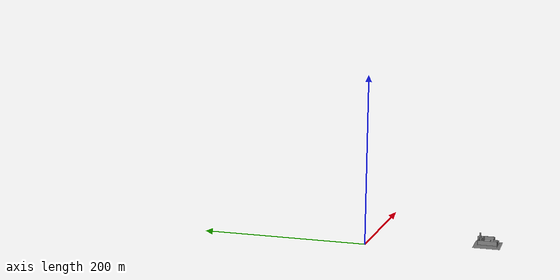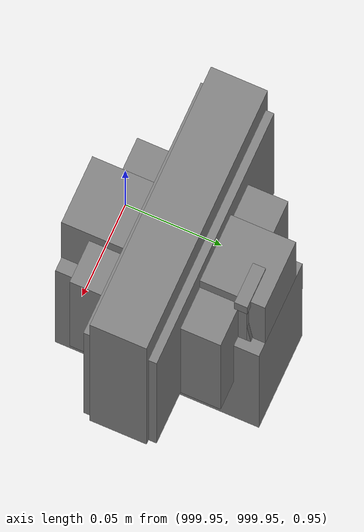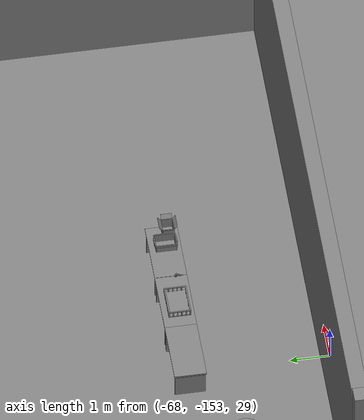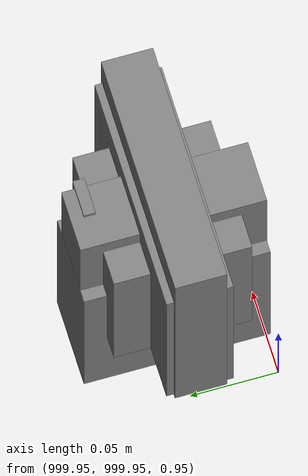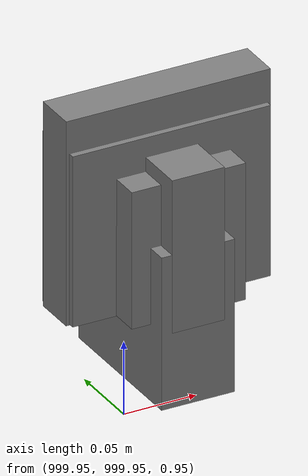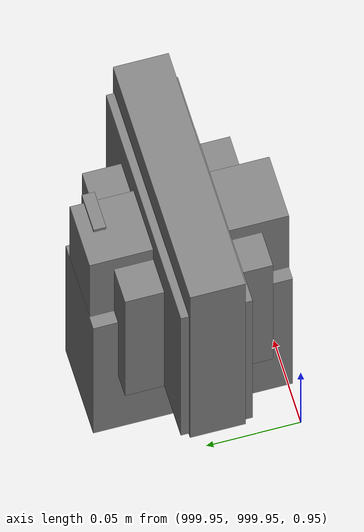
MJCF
<mujoco>
    <option gravity="0.000000000 0.000000000 -9.810000420" timestep="0.0049999999" integrator="implicitfast" density="1.225" viscosity="1.8000001e-05" noslip_iterations="10" iterations="100" sdf_iterations="50">
        <flag multiccd="disable"/>
    </option>
    <size memory="1000M"/>
    <compiler coordinate="local"/>
    <worldbody>
        <light cutoff="30" pos="0 1 1" dir="0 -1 -2"/>
        <light cutoff="30" pos="0 -1 1" dir="0 1 -2"/>
        <body pos="-64.866622925 -149.383972168 30.183746338" euler="89.999984741 89.999946594 0.000000000" name="openloong_gripper_2f85_fix_base_usda_bluebox_01">
            <geom contype="1" conaffinity="1" density="1000" type="box" material="" rgba="0.500000000 0.500000000 0.500000000 1.000000000" solimp="0.899999976 0.949999988 0.001000000" friction="1.000000000 0.005000000 0.000100000" solref="0.020000000 1.000000000" margin="0" condim="3" group="0" pos="0.276580811 0.187225342 0.000068665" quat="0.707106948 0.000077471 0.707106352 0.000077486" size="0.100000001 0.057999998 0.010000000" name="openloong_gripper_2f85_fix_base_usda_geom_DD8F053B_456A_4B29_8F48_AC5199FAE5E2"/>
            <geom contype="1" conaffinity="1" density="1000" type="box" material="" rgba="0.500000000 0.500000000 0.500000000 1.000000000" solimp="0.899999976 0.949999988 0.001000000" friction="1.000000000 0.005000000 0.000100000" solref="0.020000000 1.000000000" margin="0" condim="3" group="0" pos="0.000000000 0.002883911 0.000000000" quat="0.999999881 0.000000000 0.000000000 0.000000000" size="0.254000008 0.003000000 0.172000006" name="openloong_gripper_2f85_fix_base_usda_geom_3AEE2092_3F70_4107_B4B3_F52819A3F1CF"/>
            <geom contype="1" conaffinity="1" density="1000" type="box" material="" rgba="0.500000000 0.500000000 0.500000000 1.000000000" solimp="0.899999976 0.949999988 0.001000000" friction="1.000000000 0.005000000 0.000100000" solref="0.020000000 1.000000000" margin="0" condim="3" group="0" pos="0.000000000 0.124874115 0.173484802" quat="0.999796331 0.020176515 -0.000000015 0.000000030" size="0.259999990 0.119999997 0.007000000" name="openloong_gripper_2f85_fix_base_usda_geom_0B534FF2_7620_4F41_83B4_0272F3B6DC5B"/>
            <geom contype="1" conaffinity="1" density="1000" type="box" material="" rgba="0.500000000 0.500000000 0.500000000 1.000000000" solimp="0.899999976 0.949999988 0.001000000" friction="1.000000000 0.005000000 0.000100000" solref="0.020000000 1.000000000" margin="0" condim="3" group="0" pos="0.000000000 0.124874115 -0.173469543" quat="0.999796331 -0.020176545 -0.000000015 0.000000000" size="0.259999990 0.119999997 0.007000000" name="openloong_gripper_2f85_fix_base_usda_geom_B49F4EA7_5FFC_4518_93FE_B96128753ACD"/>
            <geom contype="1" conaffinity="1" density="1000" type="box" material="" rgba="0.500000000 0.500000000 0.500000000 1.000000000" solimp="0.899999976 0.949999988 0.001000000" friction="1.000000000 0.005000000 0.000100000" solref="0.020000000 1.000000000" margin="0" condim="3" group="0" pos="0.000000000 0.214008331 0.188980103" quat="0.999912977 0.013176724 0.000000015 0.000000000" size="0.259999990 0.029999999 0.012500000" name="openloong_gripper_2f85_fix_base_usda_geom_AF9C045A_6E4A_42B5_AB88_D1683FAF7C80"/>
            <geom contype="1" conaffinity="1" density="1000" type="box" material="" rgba="0.500000000 0.500000000 0.500000000 1.000000000" solimp="0.899999976 0.949999988 0.001000000" friction="1.000000000 0.005000000 0.000100000" solref="0.020000000 1.000000000" margin="0" condim="3" group="0" pos="-0.258361816 0.125289917 0.001876831" quat="0.702796936 -0.020792112 0.710783124 0.020769298" size="0.189999998 0.119999997 0.009000000" name="openloong_gripper_2f85_fix_base_usda_geom_968F3686_FE93_4611_9FD8_C93AEA22795A"/>
            <geom contype="1" conaffinity="1" density="1000" type="box" material="" rgba="0.500000000 0.500000000 0.500000000 1.000000000" solimp="0.899999976 0.949999988 0.001000000" friction="1.000000000 0.005000000 0.000100000" solref="0.020000000 1.000000000" margin="0" condim="3" group="0" pos="0.000000000 0.214008331 -0.188980103" quat="0.999912977 -0.013176769 0.000000030 0.000000015" size="0.259999990 0.029999999 0.012500000" name="openloong_gripper_2f85_fix_base_usda_geom_263C02F7_892F_4028_887D_495FE862BA5D"/>
            <geom contype="1" conaffinity="1" density="1000" type="box" material="" rgba="0.500000000 0.500000000 0.500000000 1.000000000" solimp="0.899999976 0.949999988 0.001000000" friction="1.000000000 0.005000000 0.000100000" solref="0.020000000 1.000000000" margin="0" condim="3" group="0" pos="-0.276611328 0.187225342 0.000068665" quat="0.707106650 0.000077441 0.707106709 0.000077456" size="0.100000001 0.057999998 0.010000000" name="openloong_gripper_2f85_fix_base_usda_geom_54129DDC_A00F_4EA8_B7D3_24080037A55C"/>
            <geom contype="1" conaffinity="1" density="1000" type="box" material="" rgba="0.500000000 0.500000000 0.500000000 1.000000000" solimp="0.899999976 0.949999988 0.001000000" friction="1.000000000 0.005000000 0.000100000" solref="0.020000000 1.000000000" margin="0" condim="3" group="0" pos="0.258331299 0.125289917 0.001876831" quat="0.702851415 0.018856421 0.710823774 -0.019329369" size="0.189999998 0.119999997 0.009000000" name="openloong_gripper_2f85_fix_base_usda_geom_45FE887A_CA67_4FFD_9E3E_AD3CB98AEEE6"/>
            <freejoint name="openloong_gripper_2f85_fix_base_usda_bluebox_01_joint"/>
            <site size="0.005000000 0.005000000 0.005000000" rgba="0.500000000 0.500000000 0.500000000 1.000000000" pos="0.000000000 0.000000000 0.000000000" quat="0.999961913 0.008726534 0.000000000 0.000000000" group="0" type="sphere" name="openloong_gripper_2f85_fix_base_usda_bluebox_01site"/>
        </body>
        <body pos="-64.496299744 -149.491867065 30.235729218" euler="0.000000000 0.000000000 89.999946594" name="openloong_gripper_2f85_fix_base_usda_cardboardbox_01">
            <geom contype="1" conaffinity="1" density="1000" type="box" material="" rgba="0.500000000 0.500000000 0.500000000 1.000000000" solimp="0.899999976 0.949999988 0.001000000" friction="1.000000000 0.005000000 0.000100000" solref="0.020000000 1.000000000" margin="0" condim="3" group="0" pos="-0.003166199 -0.004086494 0.005052090" quat="1.000000000 0.000000000 0.000000000 0.000000000" size="0.142499998 0.177500010 0.005000000" name="openloong_gripper_2f85_fix_base_usda_geom_E44F79EF_7297_4597_A4B9_6E3F7BA894C1"/>
            <geom contype="1" conaffinity="1" density="1000" type="box" material="" rgba="0.500000000 0.500000000 0.500000000 1.000000000" solimp="0.899999976 0.949999988 0.001000000" friction="1.000000000 0.005000000 0.000100000" solref="0.020000000 1.000000000" margin="0" condim="3" group="0" pos="-0.003166199 0.170316696 0.150570869" quat="1.000000000 0.000000000 0.000000000 0.000000000" size="0.142499998 0.005000000 0.149999991" name="openloong_gripper_2f85_fix_base_usda_geom_4853D398_3280_4D0A_B94B_DCEB454DB6E0"/>
            <geom contype="1" conaffinity="1" density="1000" type="box" material="" rgba="0.500000000 0.500000000 0.500000000 1.000000000" solimp="0.899999976 0.949999988 0.001000000" friction="1.000000000 0.005000000 0.000100000" solref="0.020000000 1.000000000" margin="0" condim="3" group="0" pos="-0.147399902 -0.005307198 0.150570869" quat="1.000000000 0.000000000 0.000000000 0.000000000" size="0.005000000 0.177500010 0.149999991" name="openloong_gripper_2f85_fix_base_usda_geom_890386BD_31AA_44A8_8D3A_7F7ADE922F02"/>
            <geom contype="1" conaffinity="1" density="1000" type="box" material="" rgba="0.500000000 0.500000000 0.500000000 1.000000000" solimp="0.899999976 0.949999988 0.001000000" friction="1.000000000 0.005000000 0.000100000" solref="0.020000000 1.000000000" margin="0" condim="3" group="0" pos="0.140275955 -0.005307198 0.150570869" quat="1.000000000 0.000000000 0.000000000 0.000000000" size="0.005000000 0.177500010 0.149999991" name="openloong_gripper_2f85_fix_base_usda_geom_60E966DC_7BD9_41A1_975B_EBE7FF4D8F91"/>
            <geom contype="1" conaffinity="1" density="1000" type="box" material="" rgba="0.500000000 0.500000000 0.500000000 1.000000000" solimp="0.899999976 0.949999988 0.001000000" friction="1.000000000 0.005000000 0.000100000" solref="0.020000000 1.000000000" margin="0" condim="3" group="0" pos="-0.003166199 -0.181550980 0.150570869" quat="1.000000000 0.000000000 0.000000000 0.000000000" size="0.142499998 0.005000000 0.149999991" name="openloong_gripper_2f85_fix_base_usda_geom_C9372DD4_D5BF_4487_AA91_8FCDA9ABA638"/>
            <freejoint name="openloong_gripper_2f85_fix_base_usda_cardboardbox_01_joint"/>
            <site size="0.005000000 0.005000000 0.005000000" rgba="0.500000000 0.500000000 0.500000000 1.000000000" pos="0.000000000 0.000000000 0.000000000" quat="0.999961913 0.008726535 0.000000000 0.000000000" group="0" type="sphere" name="openloong_gripper_2f85_fix_base_usda_site_4521A3A7_67C5_40E7_9632_CB55F0AC3202"/>
            <body pos="0.139160156 -0.004048347 0.301930904" euler="-179.999954224 49.383502960 179.999954224" name="openloong_gripper_2f85_fix_base_usda_A1_006">
                <geom contype="1" conaffinity="1" density="1000" type="box" material="" rgba="0.500000000 0.500000000 0.500000000 1.000000000" solimp="0.899999976 0.949999988 0.001000000" friction="1.000000000 0.005000000 0.000100000" solref="0.020000000 1.000000000" margin="0" condim="3" group="0" pos="-0.071587563 0.000009537 0.001745224" quat="0.999999881 0.000000000 0.000000000 0.000000000" size="0.071249999 0.179999992 0.002500000" name="openloong_gripper_2f85_fix_base_usda_geom_1A8B3C7B_78FB_465A_A8FC_4650422F3DF8"/>
                <joint armature="0" stiffness="0.07" damping="0.0099999998" axis="0.000000 1.000000 0.000000" type="hinge" name="openloong_gripper_2f85_fix_base_usda_A1_006"/>
            </body>
            <body pos="-0.145902634 -0.004086494 0.301938057" euler="-180.000000000 -60.000011444 -180.000000000" name="openloong_gripper_2f85_fix_base_usda_A2_006">
                <geom contype="1" conaffinity="1" density="1000" type="box" material="" rgba="0.500000000 0.500000000 0.500000000 1.000000000" solimp="0.899999976 0.949999988 0.001000000" friction="1.000000000 0.005000000 0.000100000" solref="0.020000000 1.000000000" margin="0" condim="3" group="0" pos="0.071268082 0.000009537 0.002717972" quat="0.000002921 0.000000000 -0.000000030 0.999999881" size="0.071249999 0.179999992 0.002500000" name="openloong_gripper_2f85_fix_base_usda_geom_215178CC_DF79_4D78_BB25_88B51C4B6ED4"/>
                <joint armature="0" stiffness="0.07" damping="0.0099999998" axis="0.000000 1.000000 0.000000" type="hinge" name="openloong_gripper_2f85_fix_base_usda_A2_006"/>
            </body>
            <body pos="-0.003385544 0.175991058 0.301930904" euler="-125.858116150 -0.000004561 0.000002331" name="openloong_gripper_2f85_fix_base_usda_B2_006">
                <geom contype="1" conaffinity="1" density="1000" type="box" material="" rgba="0.500000000 0.500000000 0.500000000 1.000000000" solimp="0.899999976 0.949999988 0.001000000" friction="1.000000000 0.005000000 0.000100000" solref="0.020000000 1.000000000" margin="0" condim="3" group="0" pos="0.000009537 -0.070939064 -0.002470016" quat="0.999614120 0.027776197 -0.000000015 0.000000030" size="0.137500003 0.064999998 0.005000000" name="openloong_gripper_2f85_fix_base_usda_geom_B33D20F7_9BB3_4F13_803E_E9A2DB3BD891"/>
                <joint armature="0" stiffness="0.07" damping="0.0099999998" axis="1.000000 0.000000 0.000000" type="hinge" name="openloong_gripper_2f85_fix_base_usda_B2_006"/>
            </body>
            <body pos="-0.003385544 -0.184140205 0.301938057" euler="147.805557251 0.000000000 0.000000000" name="openloong_gripper_2f85_fix_base_usda_B1_006">
                <geom contype="1" conaffinity="1" density="1000" type="box" material="" rgba="0.500000000 0.500000000 0.500000000 1.000000000" solimp="0.899999976 0.949999988 0.001000000" friction="1.000000000 0.005000000 0.000100000" solref="0.020000000 1.000000000" margin="0" condim="3" group="0" pos="-0.000028610 0.070202351 -0.002703667" quat="0.999614179 -0.027776167 0.000000000 0.000000000" size="0.137500003 0.064999998 0.005000000" name="openloong_gripper_2f85_fix_base_usda_geom_4457239D_522B_4086_9E32_668C87B3A71A"/>
                <joint armature="0" stiffness="0.07" damping="0.0099999998" axis="1.000000 0.000000 0.000000" type="hinge" name="openloong_gripper_2f85_fix_base_usda_B1_006"/>
            </body>
        </body>
        <body pos="-65.882858276 -149.481979370 30.229999542" euler="-64.487716675 0.000000000 0.000000000" name="openloong_gripper_2f85_fix_base_usda_Barcode">
            <geom contype="1" conaffinity="1" density="1000" type="box" material="" rgba="0.500000000 0.500000000 0.500000000 1.000000000" solimp="0.899999976 0.949999988 0.001000000" friction="1.000000000 0.005000000 0.000100000" solref="0.020000000 1.000000000" margin="0" condim="3" group="0" pos="0.000000000 0.013038635 0.001419067" quat="0.000000000 0.000000000 0.000000000 1.000000119" size="0.034000002 0.010000000 0.017999999" name="openloong_gripper_2f85_fix_base_usda_geom_17B16E21_B16B_45F5_9505_6D739E0D72CD"/>
            <geom contype="1" conaffinity="1" density="1000" type="box" material="" rgba="0.500000000 0.500000000 0.500000000 1.000000000" solimp="0.899999976 0.949999988 0.001000000" friction="1.000000000 0.005000000 0.000100000" solref="0.020000000 1.000000000" margin="0" condim="3" group="0" pos="0.000000000 -0.035301208 -0.007095337" quat="0.000000000 0.000000000 -0.043619365 0.999048233" size="0.028999999 0.010000000 0.020000000" name="openloong_gripper_2f85_fix_base_usda_geom_92497BAF_4000_4D2A_9890_13C86C58EAB4"/>
            <geom contype="1" conaffinity="1" density="1000" type="box" material="" rgba="0.500000000 0.500000000 0.500000000 1.000000000" solimp="0.899999976 0.949999988 0.001000000" friction="1.000000000 0.005000000 0.000100000" solref="0.020000000 1.000000000" margin="0" condim="3" group="0" pos="0.000000000 -0.043411255 -0.011749268" quat="0.922262907 0.386563420 0.000000000 0.000000000" size="0.026000001 0.010000000 0.020000000" name="openloong_gripper_2f85_fix_base_usda_geom_A340B8B2_5A08_40BF_8429_5B8CA4BCD08F"/>
            <geom contype="1" conaffinity="1" density="1000" type="box" material="" rgba="0.500000000 0.500000000 0.500000000 1.000000000" solimp="0.899999976 0.949999988 0.001000000" friction="1.000000000 0.005000000 0.000100000" solref="0.020000000 1.000000000" margin="0" condim="3" group="0" pos="0.000000000 -0.016967773 -0.031860352" quat="0.000000000 0.000000000 0.000000000 1.000000119" size="0.008000000 0.010000000 0.013000000" name="openloong_gripper_2f85_fix_base_usda_geom_B60D29AB_AD9E_4B4D_B6B6_CB266843E118"/>
            <geom contype="1" conaffinity="1" density="1000" type="box" material="" rgba="0.500000000 0.500000000 0.500000000 1.000000000" solimp="0.899999976 0.949999988 0.001000000" friction="1.000000000 0.005000000 0.000100000" solref="0.020000000 1.000000000" margin="0" condim="3" group="0" pos="0.000000000 -0.001869202 0.000312805" quat="0.953716993 0.300705761 0.000000000 0.000000000" size="0.032000002 0.010000000 0.018999999" name="openloong_gripper_2f85_fix_base_usda_geom_4DCD11D4_0DB6_464D_BF04_CE6771C6620A"/>
            <geom contype="1" conaffinity="1" density="1000" type="box" material="" rgba="0.500000000 0.500000000 0.500000000 1.000000000" solimp="0.899999976 0.949999988 0.001000000" friction="1.000000000 0.005000000 0.000100000" solref="0.020000000 1.000000000" margin="0" condim="3" group="0" pos="0.000000000 -0.019531250 -0.003173828" quat="0.953716993 0.300705761 0.000000000 0.000000000" size="0.030999999 0.010000000 0.020000000" name="openloong_gripper_2f85_fix_base_usda_geom_684F28A2_B71E_496A_8BDD_41730F0117C9"/>
            <geom contype="1" conaffinity="1" density="1000" type="box" material="" rgba="0.500000000 0.500000000 0.500000000 1.000000000" solimp="0.899999976 0.949999988 0.001000000" friction="1.000000000 0.005000000 0.000100000" solref="0.020000000 1.000000000" margin="0" condim="3" group="0" pos="0.000000000 -0.035301208 -0.007095337" quat="0.953716993 0.300705761 0.000000000 0.000000000" size="0.028999999 0.010000000 0.020000000" name="openloong_gripper_2f85_fix_base_usda_geom_AE075FBD_15C1_482D_9C7B_1DCDECAF2CFD"/>
            <geom contype="1" conaffinity="1" density="1000" type="box" material="" rgba="0.500000000 0.500000000 0.500000000 1.000000000" solimp="0.899999976 0.949999988 0.001000000" friction="1.000000000 0.005000000 0.000100000" solref="0.020000000 1.000000000" margin="0" condim="3" group="0" pos="0.000000000 -0.042617798 -0.071121216" quat="0.000000000 0.000000000 0.000000000 1.000000119" size="0.013000000 0.021000000 0.059999999" name="openloong_gripper_2f85_fix_base_usda_geom_CBFEB5D3_01A9_4688_BDCE_F73064237F10"/>
            <freejoint name="openloong_gripper_2f85_fix_base_usda_Barcode_joint"/>
            <site size="0.005000000 0.005000000 0.005000000" rgba="0.500000000 0.500000000 0.500000000 1.000000000" pos="0.000000000 0.000000000 0.000000000" quat="1.000000000 0.000000000 0.000000000 0.000000000" group="0" type="sphere" name="openloong_gripper_2f85_fix_base_usda_Barcode_site"/>
        </body>
        <body pos="-66.745018005 -149.392349243 30.184000015" euler="0.000000000 0.000000000 89.999946594" name="[22331859055389]_Basket_01">
            <geom contype="1" conaffinity="1" density="1000" type="box" material="" rgba="0.500000000 0.500000000 0.500000000 1.000000000" solimp="0.899999976 0.949999988 0.001000000" friction="1.000000000 0.005000000 0.000100000" solref="0.020000000 1.000000000" margin="0" condim="3" group="0" pos="-0.052425385 0.389207840 0.089787483" quat="0.707107008 0.000000000 0.000000000 0.707106411" size="0.014249999 0.014249999 0.059999999" name="[22331859055389]_geom_9C88FAF4_A112_4841_8D5E_8B91C62C7118"/>
            <geom contype="1" conaffinity="1" density="1000" type="box" material="" rgba="0.500000000 0.500000000 0.500000000 1.000000000" solimp="0.899999976 0.949999988 0.001000000" friction="1.000000000 0.005000000 0.000100000" solref="0.020000000 1.000000000" margin="0" condim="3" group="0" pos="0.264015198 -0.133043289 0.089787483" quat="0.707107008 0.000000000 0.000000000 0.707106411" size="0.014249999 0.014249999 0.059999999" name="[22331859055389]_geom_6E9BF886_5F38_4BA7_805A_2D8BE4A11F1D"/>
            <geom contype="1" conaffinity="1" density="1000" type="box" material="" rgba="0.500000000 0.500000000 0.500000000 1.000000000" solimp="0.899999976 0.949999988 0.001000000" friction="1.000000000 0.005000000 0.000100000" solref="0.020000000 1.000000000" margin="0" condim="3" group="0" pos="-0.264015198 -0.265548706 0.089793205" quat="0.707107008 0.000000000 0.000000000 0.707106411" size="0.014249999 0.014249999 0.059999999" name="[22331859055389]_geom_DA8529C2_4B33_4E80_B075_F376B1673AB4"/>
            <geom contype="1" conaffinity="1" density="1000" type="box" material="" rgba="0.500000000 0.500000000 0.500000000 1.000000000" solimp="0.899999976 0.949999988 0.001000000" friction="1.000000000 0.005000000 0.000100000" solref="0.020000000 1.000000000" margin="0" condim="3" group="0" pos="-0.160263062 -0.389322281 0.089793205" quat="0.707107008 0.000000000 0.000000000 0.707106411" size="0.014249999 0.014249999 0.059999999" name="[22331859055389]_geom_81CD68E7_4024_42C9_AE08_712821292452"/>
            <geom contype="1" conaffinity="1" density="1000" type="box" material="" rgba="0.500000000 0.500000000 0.500000000 1.000000000" solimp="0.899999976 0.949999988 0.001000000" friction="1.000000000 0.005000000 0.000100000" solref="0.020000000 1.000000000" margin="0" condim="3" group="0" pos="0.162265778 -0.389322281 0.089787483" quat="0.707107008 0.000000000 0.000000000 0.707106411" size="0.014249999 0.014249999 0.059999999" name="[22331859055389]_geom_274A030D_6C55_4E06_91A2_C2EEC2994064"/>
            <geom contype="1" conaffinity="1" density="1000" type="box" material="" rgba="0.500000000 0.500000000 0.500000000 1.000000000" solimp="0.899999976 0.949999988 0.001000000" friction="1.000000000 0.005000000 0.000100000" solref="0.020000000 1.000000000" margin="0" condim="3" group="0" pos="0.264015198 0.389207840 0.089787483" quat="0.707107008 0.000000000 0.000000000 0.707106411" size="0.014249999 0.014249999 0.059999999" name="[22331859055389]_geom_CD231B98_0605_4A3F_B9ED_F906927D171B"/>
            <geom contype="1" conaffinity="1" density="1000" type="box" material="" rgba="0.500000000 0.500000000 0.500000000 1.000000000" solimp="0.899999976 0.949999988 0.001000000" friction="1.000000000 0.005000000 0.000100000" solref="0.020000000 1.000000000" margin="0" condim="3" group="0" pos="-0.264015198 -0.133043289 0.089793205" quat="0.707107008 0.000000000 0.000000000 0.707106411" size="0.014249999 0.014249999 0.059999999" name="[22331859055389]_geom_14A55B50_94FA_4F39_B648_F5041EA0C44A"/>
            <geom contype="1" conaffinity="1" density="1000" type="box" material="" rgba="0.500000000 0.500000000 0.500000000 1.000000000" solimp="0.899999976 0.949999988 0.001000000" friction="1.000000000 0.005000000 0.000100000" solref="0.020000000 1.000000000" margin="0" condim="3" group="0" pos="-0.264026642 0.269256592 0.089793205" quat="0.707107008 0.000000000 0.000000000 0.707106411" size="0.014249999 0.014249999 0.059999999" name="[22331859055389]_geom_73FEC9E1_AA2C_4783_A328_EE29A527BFFF"/>
            <geom contype="1" conaffinity="1" density="1000" type="box" material="" rgba="0.500000000 0.500000000 0.500000000 1.000000000" solimp="0.899999976 0.949999988 0.001000000" friction="1.000000000 0.005000000 0.000100000" solref="0.020000000 1.000000000" margin="0" condim="3" group="0" pos="0.054462433 0.389207840 0.089787483" quat="0.707107008 0.000000000 0.000000000 0.707106411" size="0.014249999 0.014249999 0.059999999" name="[22331859055389]_geom_E06101C5_E976_44C5_A646_E2F5B787FD92"/>
            <geom contype="1" conaffinity="1" density="1000" type="box" material="" rgba="0.500000000 0.500000000 0.500000000 1.000000000" solimp="0.899999976 0.949999988 0.001000000" friction="1.000000000 0.005000000 0.000100000" solref="0.020000000 1.000000000" margin="0" condim="3" group="0" pos="0.054462433 -0.389322281 0.089787483" quat="0.707107008 0.000000000 0.000000000 0.707106411" size="0.014249999 0.014249999 0.059999999" name="[22331859055389]_geom_EB5096AB_FA2F_48EC_8122_C99B4D068BE5"/>
            <geom contype="1" conaffinity="1" density="1000" type="box" material="" rgba="0.500000000 0.500000000 0.500000000 1.000000000" solimp="0.899999976 0.949999988 0.001000000" friction="1.000000000 0.005000000 0.000100000" solref="0.020000000 1.000000000" margin="0" condim="3" group="0" pos="0.264015198 0.269256592 0.089793205" quat="0.707107008 0.000000000 0.000000000 0.707106411" size="0.014249999 0.014249999 0.059999999" name="[22331859055389]_geom_A08D9B33_DD80_4C07_AA6B_5374BBB6AAA4"/>
            <geom contype="1" conaffinity="1" density="1000" type="box" material="" rgba="0.500000000 0.500000000 0.500000000 1.000000000" solimp="0.899999976 0.949999988 0.001000000" friction="1.000000000 0.005000000 0.000100000" solref="0.020000000 1.000000000" margin="0" condim="3" group="0" pos="0.264015198 -0.389322281 0.089787483" quat="0.707107008 0.000000000 0.000000000 0.707106411" size="0.014249999 0.014249999 0.059999999" name="[22331859055389]_geom_8780DFF2_93A3_4486_83BF_BFB4ECA0A6E3"/>
            <geom contype="1" conaffinity="1" density="1000" type="box" material="" rgba="0.500000000 0.500000000 0.500000000 1.000000000" solimp="0.899999976 0.949999988 0.001000000" friction="1.000000000 0.005000000 0.000100000" solref="0.020000000 1.000000000" margin="0" condim="3" group="0" pos="0.000000000 0.000000000 0.015998840" quat="0.707107008 0.000000000 0.000000000 0.707106411" size="0.403499991 0.279000014 0.015750000" name="[22331859055389]_geom_3338081F_9C83_4477_A724_E2E0F3999956"/>
            <geom contype="1" conaffinity="1" density="1000" type="box" material="" rgba="0.500000000 0.500000000 0.500000000 1.000000000" solimp="0.899999976 0.949999988 0.001000000" friction="1.000000000 0.005000000 0.000100000" solref="0.020000000 1.000000000" margin="0" condim="3" group="0" pos="0.000000000 -0.389476776 0.163619041" quat="0.707107008 0.000000000 0.000000000 0.707106411" size="0.015000000 0.277500004 0.015750000" name="[22331859055389]_geom_E6A3FA6B_F565_42A1_9260_C7FA47C95D89"/>
            <geom contype="1" conaffinity="1" density="1000" type="box" material="" rgba="0.500000000 0.500000000 0.500000000 1.000000000" solimp="0.899999976 0.949999988 0.001000000" friction="1.000000000 0.005000000 0.000100000" solref="0.020000000 1.000000000" margin="0" condim="3" group="0" pos="0.162265778 0.389207840 0.089787483" quat="0.707107008 0.000000000 0.000000000 0.707106411" size="0.014249999 0.014249999 0.059999999" name="[22331859055389]_geom_420DE014_0582_4F68_9EB6_73A49C4EA665"/>
            <geom contype="1" conaffinity="1" density="1000" type="box" material="" rgba="0.500000000 0.500000000 0.500000000 1.000000000" solimp="0.899999976 0.949999988 0.001000000" friction="1.000000000 0.005000000 0.000100000" solref="0.020000000 1.000000000" margin="0" condim="3" group="0" pos="0.000000000 0.389471054 0.163619041" quat="0.707107008 0.000000000 0.000000000 0.707106411" size="0.015000000 0.277500004 0.015750000" name="[22331859055389]_geom_DE5C9A61_AB38_4024_B81D_2E6B82755554"/>
            <geom contype="1" conaffinity="1" density="1000" type="box" material="" rgba="0.500000000 0.500000000 0.500000000 1.000000000" solimp="0.899999976 0.949999988 0.001000000" friction="1.000000000 0.005000000 0.000100000" solref="0.020000000 1.000000000" margin="0" condim="3" group="0" pos="-0.263511658 0.000000000 0.163619041" quat="0.707107008 0.000000000 0.000000000 0.707106411" size="0.403499991 0.015000000 0.015750000" name="[22331859055389]_geom_A0D5EE2A_FF7F_4A1E_94D8_098F1E9A2356"/>
            <geom contype="1" conaffinity="1" density="1000" type="box" material="" rgba="0.500000000 0.500000000 0.500000000 1.000000000" solimp="0.899999976 0.949999988 0.001000000" friction="1.000000000 0.005000000 0.000100000" solref="0.020000000 1.000000000" margin="0" condim="3" group="0" pos="-0.264015198 0.141334534 0.089793205" quat="0.707107008 0.000000000 0.000000000 0.707106411" size="0.014249999 0.014249999 0.059999999" name="[22331859055389]_geom_C756CAA1_EF25_47FC_B59F_750DBC7B9770"/>
            <geom contype="1" conaffinity="1" density="1000" type="box" material="" rgba="0.500000000 0.500000000 0.500000000 1.000000000" solimp="0.899999976 0.949999988 0.001000000" friction="1.000000000 0.005000000 0.000100000" solref="0.020000000 1.000000000" margin="0" condim="3" group="0" pos="0.264015198 -0.265548706 0.089787483" quat="0.707107008 0.000000000 0.000000000 0.707106411" size="0.014249999 0.014249999 0.059999999" name="[22331859055389]_geom_864020F1_C1C3_4FC9_8EC6_A854CFE52C09"/>
            <geom contype="1" conaffinity="1" density="1000" type="box" material="" rgba="0.500000000 0.500000000 0.500000000 1.000000000" solimp="0.899999976 0.949999988 0.001000000" friction="1.000000000 0.005000000 0.000100000" solref="0.020000000 1.000000000" margin="0" condim="3" group="0" pos="-0.160263062 0.389207840 0.089787483" quat="0.707107008 0.000000000 0.000000000 0.707106411" size="0.014249999 0.014249999 0.059999999" name="[22331859055389]_geom_8705D460_8D42_451D_A3D4_50DDCA085A2C"/>
            <geom contype="1" conaffinity="1" density="1000" type="box" material="" rgba="0.500000000 0.500000000 0.500000000 1.000000000" solimp="0.899999976 0.949999988 0.001000000" friction="1.000000000 0.005000000 0.000100000" solref="0.020000000 1.000000000" margin="0" condim="3" group="0" pos="-0.052425385 -0.389322281 0.089787483" quat="0.707107008 0.000000000 0.000000000 0.707106411" size="0.014249999 0.014249999 0.059999999" name="[22331859055389]_geom_356956CF_9B61_4CF6_A853_3E48CAA56DD3"/>
            <geom contype="1" conaffinity="1" density="1000" type="box" material="" rgba="0.500000000 0.500000000 0.500000000 1.000000000" solimp="0.899999976 0.949999988 0.001000000" friction="1.000000000 0.005000000 0.000100000" solref="0.020000000 1.000000000" margin="0" condim="3" group="0" pos="-0.264026642 -0.389322281 0.089793205" quat="0.707107008 0.000000000 0.000000000 0.707106411" size="0.014249999 0.014249999 0.059999999" name="[22331859055389]_geom_853053AA_DB8A_4C4B_94B7_CFCAE54CA97C"/>
            <geom contype="1" conaffinity="1" density="1000" type="box" material="" rgba="0.500000000 0.500000000 0.500000000 1.000000000" solimp="0.899999976 0.949999988 0.001000000" friction="1.000000000 0.005000000 0.000100000" solref="0.020000000 1.000000000" margin="0" condim="3" group="0" pos="0.264015198 0.141334534 0.089787483" quat="0.707107008 0.000000000 0.000000000 0.707106411" size="0.014249999 0.014249999 0.059999999" name="[22331859055389]_geom_C540841C_07A9_4940_8EDE_968E4B357061"/>
            <geom contype="1" conaffinity="1" density="1000" type="box" material="" rgba="0.500000000 0.500000000 0.500000000 1.000000000" solimp="0.899999976 0.949999988 0.001000000" friction="1.000000000 0.005000000 0.000100000" solref="0.020000000 1.000000000" margin="0" condim="3" group="0" pos="-0.264015198 0.389207840 0.089793205" quat="0.707107008 0.000000000 0.000000000 0.707106411" size="0.014249999 0.014249999 0.059999999" name="[22331859055389]_geom_C48601BF_EB4F_418C_998E_4BB4D973DE97"/>
            <geom contype="1" conaffinity="1" density="1000" type="box" material="" rgba="0.500000000 0.500000000 0.500000000 1.000000000" solimp="0.899999976 0.949999988 0.001000000" friction="1.000000000 0.005000000 0.000100000" solref="0.020000000 1.000000000" margin="0" condim="3" group="0" pos="0.264015198 0.004480362 0.089787483" quat="0.707107008 0.000000000 0.000000000 0.707106411" size="0.014249999 0.014249999 0.059999999" name="[22331859055389]_geom_38C1E8D1_C566_4E68_BD3A_515136F0870D"/>
            <geom contype="1" conaffinity="1" density="1000" type="box" material="" rgba="0.500000000 0.500000000 0.500000000 1.000000000" solimp="0.899999976 0.949999988 0.001000000" friction="1.000000000 0.005000000 0.000100000" solref="0.020000000 1.000000000" margin="0" condim="3" group="0" pos="0.263694763 -0.000011444 0.163619041" quat="0.707107008 0.000000000 0.000000000 0.707106411" size="0.403499991 0.015000000 0.015750000" name="[22331859055389]_geom_651F814C_308B_4B11_AD8D_4E00CCD20C54"/>
            <geom contype="1" conaffinity="1" density="1000" type="box" material="" rgba="0.500000000 0.500000000 0.500000000 1.000000000" solimp="0.899999976 0.949999988 0.001000000" friction="1.000000000 0.005000000 0.000100000" solref="0.020000000 1.000000000" margin="0" condim="3" group="0" pos="-0.264015198 0.004480362 0.089793205" quat="0.707107008 0.000000000 0.000000000 0.707106411" size="0.014249999 0.014249999 0.059999999" name="[22331859055389]_geom_CE96A307_835D_43B5_A8DA_845E4578910C"/>
            <freejoint name="[22331859055389]_joint_60A1B410_1898_48B5_8B40_3536B40FA50D"/>
        </body>
        <body pos="0.000000000 0.000000000 0.000000000" euler="0.000000000 0.000000000 0.000000000" name="Static Objects_Static Objects">
            <geom contype="1" conaffinity="1" density="1000" type="box" material="" rgba="0.500000000 0.500000000 0.500000000 1.000000000" solimp="0.899999976 0.949999988 0.001000000" friction="1.000000000 0.005000000 0.000100000" solref="0.020000000 1.000000000" margin="0" condim="3" group="0" pos="-67.544113159 -149.365814209 29.727830887" quat="0.500000417 0.499999970 0.499999553 0.499999970" size="0.381000012 0.319999993 0.041000001" name="Static Objects_geom_2E68AB93_E211_4782_9D5C_7CB0B5DF3761"/>
            <geom contype="1" conaffinity="1" density="1000" type="box" material="" rgba="0.500000000 0.500000000 0.500000000 1.000000000" solimp="0.899999976 0.949999988 0.001000000" friction="1.000000000 0.005000000 0.000100000" solref="0.020000000 1.000000000" margin="0" condim="3" group="0" pos="-68.239501953 -149.365814209 30.086868286" quat="0.500000417 0.499999970 0.499999553 0.499999970" size="0.370999992 0.039500002 0.745000005" name="Static Objects_geom_F8C7BE5E_2725_4E63_9963_1FFCC39A0952"/>
            <geom contype="1" conaffinity="1" density="1000" type="box" material="" rgba="0.500000000 0.500000000 0.500000000 1.000000000" solimp="0.899999976 0.949999988 0.001000000" friction="1.000000000 0.005000000 0.000100000" solref="0.020000000 1.000000000" margin="0" condim="3" group="0" pos="-68.239501953 -149.365814209 30.147235870" quat="0.500000417 0.499999970 0.499999553 0.499999970" size="0.400000006 0.022000000 0.800000012" name="Static Objects_geom_14524DFB_0A3E_4C20_A240_00B37CD64661"/>
            <geom contype="1" conaffinity="1" density="1000" type="box" material="" rgba="0.500000000 0.500000000 0.500000000 1.000000000" solimp="0.899999976 0.949999988 0.001000000" friction="1.000000000 0.005000000 0.000100000" solref="0.020000000 1.000000000" margin="0" condim="3" group="0" pos="-68.934890747 -149.365814209 29.727830887" quat="0.500000417 0.499999970 0.499999553 0.499999970" size="0.381000012 0.319999993 0.041000001" name="Static Objects_geom_FDB8F702_74F4_4781_8C5A_99582AF1A9FB"/>
            <geom contype="1" conaffinity="1" density="1000" type="box" material="" rgba="0.500000000 0.500000000 0.500000000 1.000000000" solimp="0.899999976 0.949999988 0.001000000" friction="1.000000000 0.005000000 0.000100000" solref="0.020000000 1.000000000" margin="0" condim="3" group="0" pos="-68.239501953 -149.365814209 29.561563492" quat="0.500000417 0.499999970 0.499999553 0.499999970" size="0.020000000 0.022000000 0.660000026" name="Static Objects_geom_9CA91D17_69BA_4DE8_94BB_F95D21B49D57"/>
            <geom contype="1" conaffinity="1" density="1000" type="box" material="" rgba="0.500000000 0.500000000 0.500000000 1.000000000" solimp="0.899999976 0.949999988 0.001000000" friction="1.000000000 0.005000000 0.000100000" solref="0.020000000 1.000000000" margin="0" condim="3" group="0" pos="-65.945671082 -149.365814209 29.727830887" quat="0.500000417 0.499999970 0.499999553 0.499999970" size="0.381000012 0.319999993 0.041000001" name="Static Objects_geom_D80E41F9_B983_4EB9_AE9D_97E8C307826E"/>
            <geom contype="1" conaffinity="1" density="1000" type="box" material="" rgba="0.500000000 0.500000000 0.500000000 1.000000000" solimp="0.899999976 0.949999988 0.001000000" friction="1.000000000 0.005000000 0.000100000" solref="0.020000000 1.000000000" margin="0" condim="3" group="0" pos="-66.641059875 -149.365814209 30.086868286" quat="0.500000417 0.499999970 0.499999553 0.499999970" size="0.370999992 0.039500002 0.745000005" name="Static Objects_geom_3A35AAC0_1990_4F01_B672_212CD064F11E"/>
            <geom contype="1" conaffinity="1" density="1000" type="box" material="" rgba="0.500000000 0.500000000 0.500000000 1.000000000" solimp="0.899999976 0.949999988 0.001000000" friction="1.000000000 0.005000000 0.000100000" solref="0.020000000 1.000000000" margin="0" condim="3" group="0" pos="-66.641059875 -149.365814209 30.147235870" quat="0.500000417 0.499999970 0.499999553 0.499999970" size="0.400000006 0.022000000 0.800000012" name="Static Objects_geom_4768642E_AD54_45D3_A8F0_66C0037505EE"/>
            <geom contype="1" conaffinity="1" density="1000" type="box" material="" rgba="0.500000000 0.500000000 0.500000000 1.000000000" solimp="0.899999976 0.949999988 0.001000000" friction="1.000000000 0.005000000 0.000100000" solref="0.020000000 1.000000000" margin="0" condim="3" group="0" pos="-67.336448669 -149.365814209 29.727830887" quat="0.500000417 0.499999970 0.499999553 0.499999970" size="0.381000012 0.319999993 0.041000001" name="Static Objects_geom_93493BF4_537F_4E5C_8066_1C780E5299E3"/>
            <geom contype="1" conaffinity="1" density="1000" type="box" material="" rgba="0.500000000 0.500000000 0.500000000 1.000000000" solimp="0.899999976 0.949999988 0.001000000" friction="1.000000000 0.005000000 0.000100000" solref="0.020000000 1.000000000" margin="0" condim="3" group="0" pos="-66.641059875 -149.365814209 29.561563492" quat="0.500000417 0.499999970 0.499999553 0.499999970" size="0.020000000 0.022000000 0.660000026" name="Static Objects_geom_332E902D_7B0D_4C29_87E5_9C8DCE567132"/>
            <geom contype="1" conaffinity="1" density="1000" type="box" material="" rgba="0.500000000 0.500000000 0.500000000 1.000000000" solimp="0.899999976 0.949999988 0.001000000" friction="1.000000000 0.005000000 0.000100000" solref="0.020000000 1.000000000" margin="0" condim="3" group="0" pos="-64.338577271 -149.365814209 29.727830887" quat="0.500000417 0.499999970 0.499999553 0.499999970" size="0.381000012 0.319999993 0.041000001" name="Static Objects_geom_F3F2DE02_ACCA_43D2_9079_E12AF64F60F8"/>
            <geom contype="1" conaffinity="1" density="1000" type="box" material="" rgba="0.500000000 0.500000000 0.500000000 1.000000000" solimp="0.899999976 0.949999988 0.001000000" friction="1.000000000 0.005000000 0.000100000" solref="0.020000000 1.000000000" margin="0" condim="3" group="0" pos="-65.033966064 -149.365814209 30.086868286" quat="0.500000417 0.499999970 0.499999553 0.499999970" size="0.370999992 0.039500002 0.745000005" name="Static Objects_geom_64801B23_56AC_48F5_A405_4DA7A2375E56"/>
            <geom contype="1" conaffinity="1" density="1000" type="box" material="" rgba="0.500000000 0.500000000 0.500000000 1.000000000" solimp="0.899999976 0.949999988 0.001000000" friction="1.000000000 0.005000000 0.000100000" solref="0.020000000 1.000000000" margin="0" condim="3" group="0" pos="-65.033966064 -149.365814209 30.147235870" quat="0.500000417 0.499999970 0.499999553 0.499999970" size="0.400000006 0.022000000 0.800000012" name="Static Objects_geom_D549309A_2AF7_4BF2_A402_6C084480866C"/>
            <geom contype="1" conaffinity="1" density="1000" type="box" material="" rgba="0.500000000 0.500000000 0.500000000 1.000000000" solimp="0.899999976 0.949999988 0.001000000" friction="1.000000000 0.005000000 0.000100000" solref="0.020000000 1.000000000" margin="0" condim="3" group="0" pos="-65.729354858 -149.365814209 29.727830887" quat="0.500000417 0.499999970 0.499999553 0.499999970" size="0.381000012 0.319999993 0.041000001" name="Static Objects_geom_50B8E669_A0CD_45BE_8A07_C45B03B8C9DC"/>
            <geom contype="1" conaffinity="1" density="1000" type="box" material="" rgba="0.500000000 0.500000000 0.500000000 1.000000000" solimp="0.899999976 0.949999988 0.001000000" friction="1.000000000 0.005000000 0.000100000" solref="0.020000000 1.000000000" margin="0" condim="3" group="0" pos="-65.033966064 -149.365814209 29.561563492" quat="0.500000417 0.499999970 0.499999553 0.499999970" size="0.020000000 0.022000000 0.660000026" name="Static Objects_geom_C9688538_D6B7_4004_B1FF_82501F65E87F"/>
            <geom contype="1" conaffinity="1" density="1000" type="box" material="" rgba="0.500000000 0.500000000 0.500000000 1.000000000" solimp="0.899999976 0.949999988 0.001000000" friction="1.000000000 0.005000000 0.000100000" solref="0.020000000 1.000000000" margin="0" condim="3" group="0" pos="-61.754566193 -137.853729248 33.906845093" quat="0.707107067 0.000000000 0.000000000 0.707106471" size="0.759999990 0.759999990 4.500000000" name="Static Objects_geom_C58FA0B9_E75C_4795_AE10_DAF241971B9D"/>
            <geom contype="1" conaffinity="1" density="1000" type="box" material="" rgba="0.500000000 0.500000000 0.500000000 1.000000000" solimp="0.899999976 0.949999988 0.001000000" friction="1.000000000 0.005000000 0.000100000" solref="0.020000000 1.000000000" margin="0" condim="3" group="0" pos="-57.511135101 -144.927108765 31.707921982" quat="1.000000000 0.000000000 0.000000000 0.000000000" size="0.200000003 8.000000000 2.299999952" name="Static Objects_geom_B469C78B_6D57_453B_87E4_173DEC2B5397"/>
            <geom contype="1" conaffinity="1" density="1000" type="box" material="" rgba="0.500000000 0.500000000 0.500000000 1.000000000" solimp="0.899999976 0.949999988 0.001000000" friction="1.000000000 0.005000000 0.000100000" solref="0.020000000 1.000000000" margin="0" condim="3" group="0" pos="-80.517646790 -157.574050903 31.688196182" quat="0.707107067 0.000000000 0.000000000 0.707106471" size="0.600000024 0.600000024 2.299999952" name="Static Objects_geom_B79953BA_1A66_4662_8F66_44190A10D5DB"/>
            <geom contype="1" conaffinity="1" density="1000" type="box" material="" rgba="0.500000000 0.500000000 0.500000000 1.000000000" solimp="0.899999976 0.949999988 0.001000000" friction="1.000000000 0.005000000 0.000100000" solref="0.020000000 1.000000000" margin="0" condim="3" group="0" pos="-80.711044312 -147.414932251 31.666158676" quat="1.000000000 0.000000000 0.000000000 0.000000000" size="0.200000003 10.000000000 2.299999952" name="Static Objects_geom_F482FF75_8DD4_4D7F_B8DE_E5FE99C224FB"/>
            <geom contype="1" conaffinity="1" density="1000" type="box" material="" rgba="0.500000000 0.500000000 0.500000000 1.000000000" solimp="0.899999976 0.949999988 0.001000000" friction="1.000000000 0.005000000 0.000100000" solref="0.020000000 1.000000000" margin="0" condim="3" group="0" pos="-57.687217712 -137.434692383 31.688196182" quat="0.707107067 0.000000000 0.000000000 0.707106471" size="0.600000024 0.600000024 2.299999952" name="Static Objects_geom_139A74BA_F5CD_43AF_B280_2FF4C0977CF7"/>
            <geom contype="1" conaffinity="1" density="1000" type="box" material="" rgba="0.500000000 0.500000000 0.500000000 1.000000000" solimp="0.899999976 0.949999988 0.001000000" friction="1.000000000 0.005000000 0.000100000" solref="0.020000000 1.000000000" margin="0" condim="3" group="0" pos="-69.537033081 -140.263229370 31.714921951" quat="0.707107067 0.000000000 0.000000000 0.707106471" size="0.759999990 4.500000000 2.299999952" name="Static Objects_geom_0E53101E_A7F7_4F2F_A866_B85C4251F658"/>
            <geom contype="1" conaffinity="1" density="1000" type="box" material="" rgba="0.500000000 0.500000000 0.500000000 1.000000000" solimp="0.899999976 0.949999988 0.001000000" friction="1.000000000 0.005000000 0.000100000" solref="0.020000000 1.000000000" margin="0" condim="3" group="0" pos="-80.073638916 -137.853713989 33.906845093" quat="0.707107067 0.000000000 0.000000000 0.707106471" size="0.759999990 0.759999990 4.500000000" name="Static Objects_geom_358196EA_1B11_4AC1_8B3C_4B1B40A27EB0"/>
            <geom contype="1" conaffinity="1" density="1000" type="box" material="" rgba="0.500000000 0.500000000 0.500000000 1.000000000" solimp="0.899999976 0.949999988 0.001000000" friction="1.000000000 0.005000000 0.000100000" solref="0.020000000 1.000000000" margin="0" condim="3" group="0" pos="-73.406707764 -155.734664917 31.707921982" quat="1.000000000 0.000000000 0.000000000 0.000000000" size="0.200000003 3.000000000 2.299999952" name="Static Objects_geom_31F50951_83D8_4596_8F4C_C8923AE614BD"/>
            <geom contype="1" conaffinity="1" density="1000" type="box" material="" rgba="0.500000000 0.500000000 0.500000000 1.000000000" solimp="0.899999976 0.949999988 0.001000000" friction="1.000000000 0.005000000 0.000100000" solref="0.020000000 1.000000000" margin="0" condim="3" group="0" pos="-68.497543335 -137.448257446 31.707921982" quat="0.707107067 0.000000000 0.000000000 0.707106471" size="0.200000003 14.000000000 2.299999952" name="Static Objects_geom_435400E9_4B3B_4A66_B116_D7886CE8924F"/>
            <geom contype="1" conaffinity="1" density="1000" type="cylinder" material="" rgba="0.500000000 0.500000000 0.500000000 1.000000000" solimp="0.899999976 0.949999988 0.001000000" friction="1.000000000 0.005000000 0.000100000" solref="0.020000000 1.000000000" margin="0" condim="3" group="0" pos="-68.868522644 -142.134506226 31.711090088" quat="0.707107067 0.000000000 0.000000000 0.707106471" size="0.509999990 2.299999952 1.000000000" name="Static Objects_geom_271FDE51_3EE7_4770_A686_8DD5640266D1"/>
            <geom contype="1" conaffinity="1" density="1000" type="plane" material="" rgba="0.500000000 0.500000000 0.500000000 1.000000000" solimp="0.899999976 0.949999988 0.001000000" friction="1.000000000 0.005000000 0.000100000" solref="0.020000000 1.000000000" margin="0" condim="3" group="0" pos="-72.873703003 -147.131927490 29.409669876" quat="1.000000000 0.000000000 0.000000000 0.000000000" size="18.000000000 14.000000000 1.000000000" name="Static Objects_geom_472A7851_C3A9_42CF_A658_D78D70F665E7"/>
            <geom contype="1" conaffinity="1" density="1000" type="box" material="" rgba="0.500000000 0.500000000 0.500000000 1.000000000" solimp="0.899999976 0.949999988 0.001000000" friction="1.000000000 0.005000000 0.000100000" solref="0.020000000 1.000000000" margin="0" condim="3" group="0" pos="-79.943580627 -157.782272339 31.707921982" quat="0.707107067 0.000000000 0.000000000 0.707106471" size="0.200000003 7.000000000 2.299999952" name="Static Objects_geom_E0AE4C35_9B26_4AA8_B589_73984E3A13C9"/>
            <geom contype="1" conaffinity="1" density="1000" type="box" material="" rgba="0.500000000 0.500000000 0.500000000 1.000000000" solimp="0.899999976 0.949999988 0.001000000" friction="1.000000000 0.005000000 0.000100000" solref="0.020000000 1.000000000" margin="0" condim="3" group="0" pos="-65.421028137 -152.903442383 31.707921982" quat="0.707107067 0.000000000 0.000000000 0.707106471" size="0.200000003 7.800000191 2.299999952" name="Static Objects_geom_46BBBCCA_BC60_4D85_88A9_B078F67F3D86"/>
            <geom contype="1" conaffinity="1" density="1000" type="box" material="" rgba="0.500000000 0.500000000 0.500000000 1.000000000" solimp="0.899999976 0.949999988 0.001000000" friction="1.000000000 0.005000000 0.000100000" solref="0.020000000 1.000000000" margin="0" condim="3" group="0" pos="-74.776908875 -149.964416504 31.688196182" quat="1.000000000 0.000000000 0.000000000 0.000000000" size="0.600000024 0.409999996 2.299999952" name="Static Objects_geom_EBC2CF7A_427C_479C_B248_9B7226A95939"/>
            <geom contype="1" conaffinity="1" density="1000" type="cylinder" material="" rgba="0.500000000 0.500000000 0.500000000 1.000000000" solimp="0.899999976 0.949999988 0.001000000" friction="1.000000000 0.005000000 0.000100000" solref="0.020000000 1.000000000" margin="0" condim="3" group="0" pos="-60.161884308 -142.134506226 31.711090088" quat="0.707107067 0.000000000 0.000000000 0.707106471" size="0.509999990 2.299999952 1.000000000" name="Static Objects_geom_DDFFE9D2_A4B3_4099_B862_3E6048140155"/>
            <geom contype="1" conaffinity="1" density="1000" type="cylinder" material="" rgba="0.500000000 0.500000000 0.500000000 1.000000000" solimp="0.899999976 0.949999988 0.001000000" friction="1.000000000 0.005000000 0.000100000" solref="0.020000000 1.000000000" margin="0" condim="3" group="0" pos="-75.382453918 -149.963455200 31.711090088" quat="0.707107067 0.000000000 0.000000000 0.707106471" size="0.409999996 2.299999952 1.000000000" name="Static Objects_geom_61113E08_0275_4DC5_8C54_6DE4CE1D2985"/>
            <geom contype="1" conaffinity="1" density="1000" type="cylinder" material="" rgba="0.500000000 0.500000000 0.500000000 1.000000000" solimp="0.899999976 0.949999988 0.001000000" friction="1.000000000 0.005000000 0.000100000" solref="0.020000000 1.000000000" margin="0" condim="3" group="0" pos="-74.154960632 -149.963455200 31.711090088" quat="0.707107067 0.000000000 0.000000000 0.707106471" size="0.409999996 2.299999952 1.000000000" name="Static Objects_geom_FD1F095D_8918_4824_9FAC_B7D1D2D2A6A5"/>
            <geom contype="1" conaffinity="1" density="1000" type="cylinder" material="" rgba="0.500000000 0.500000000 0.500000000 1.000000000" solimp="0.899999976 0.949999988 0.001000000" friction="1.000000000 0.005000000 0.000100000" solref="0.020000000 1.000000000" margin="0" condim="3" group="0" pos="-77.566612244 -142.134506226 31.711090088" quat="0.707107067 0.000000000 0.000000000 0.707106471" size="0.509999990 2.299999952 1.000000000" name="Static Objects_geom_B40DA932_6830_4C81_A95D_6805FE009A60"/>
        </body>
        <body pos="1000.000000000 1000.000000000 1.000000000" euler="0.000000000 0.000000000 180.000000000" name="openloong_gripper_2f85_fix_base_usda_cpu_fan">
            <geom contype="1" conaffinity="1" density="1000" type="box" material="" rgba="0.500000000 0.500000000 0.500000000 1.000000000" solimp="0.899999976 0.949999988 0.001000000" friction="1.000000000 0.005000000 0.000100000" solref="0.020000000 1.000000000" margin="0" condim="3" group="0" pos="0.000000000 0.000000000 0.070034981" quat="0.000000000 0.000000000 0.000000000 1.000000000" size="0.070700005 0.014699999 0.070700005" name="openloong_gripper_2f85_fix_base_usda_geom_10785E1A_DFCD_41E1_BD44_B10E598C9782"/>
            <freejoint name="openloong_gripper_2f85_fix_base_usda_cpu_fan_joint"/>
            <site size="0.005000000 0.005000000 0.005000000" rgba="0.500000000 0.500000000 0.500000000 1.000000000" pos="0.000000000 0.000000000 0.000000000" quat="0.999961913 0.008726535 0.000000000 0.000000000" group="0" type="sphere" name="openloong_gripper_2f85_fix_base_usda_cpu_fancsite"/>
        </body>
        <body pos="-65.989212036 -149.399887085 31.162664413" euler="132.781738281 65.760139465 -117.199562073" mocap="true" name="spotlight3_SpotLight"/>
        <body pos="1000.000000000 1000.000000000 1.000000000" euler="0.000011953 0.000005123 -179.999984741" name="openloong_gripper_2f85_fix_base_usda_intel_box">
            <geom contype="1" conaffinity="1" density="1000" type="box" material="" rgba="0.500000000 0.500000000 0.500000000 1.000000000" solimp="0.899999976 0.949999988 0.001000000" friction="1.000000000 0.005000000 0.000100000" solref="0.020000000 1.000000000" margin="0" condim="3" group="0" pos="0.000000000 -0.000067139 0.000082284" quat="0.707106709 0.000000225 0.000000253 0.707106650" size="0.052800003 0.025300000 0.052800003" name="openloong_gripper_2f85_fix_base_usda_geom_5B4CFDA4_A659_4B34_B186_C4070D761192"/>
            <freejoint name="openloong_gripper_2f85_fix_base_usda_intel_box_joint"/>
            <site size="0.005000000 0.005000000 0.005000000" rgba="0.500000000 0.500000000 0.500000000 1.000000000" pos="0.000000000 0.000000000 0.000000000" quat="0.999961913 0.008726500 0.000000000 0.000000000" group="0" type="sphere" name="openloong_gripper_2f85_fix_base_usda_intel_boxsite"/>
        </body>
        <body pos="-65.941154480 -148.911117554 31.170751572" euler="144.960433960 47.910232544 -109.058837891" mocap="true" name="spotlight1_SpotLight"/>
        <body pos="1000.000000000 999.999938965 1.000000000" euler="0.000000000 0.000000000 180.000000000" name="openloong_gripper_2f85_fix_base_usda_intelcore_i5">
            <geom contype="1" conaffinity="1" density="1000" type="box" material="" rgba="0.500000000 0.500000000 0.500000000 1.000000000" solimp="0.899999976 0.949999988 0.001000000" friction="1.000000000 0.005000000 0.000100000" solref="0.020000000 1.000000000" margin="0" condim="3" group="0" pos="0.000000000 0.000000000 0.051722717" quat="0.707106709 0.000000000 0.000000000 -0.707106769" size="0.052800000 0.018080002 0.052800000" name="openloong_gripper_2f85_fix_base_usda_geom_18A109A0_8097_4E52_868D_9314D98CF6A7"/>
            <freejoint name="openloong_gripper_2f85_fix_base_usda_intelcore_i5_joint"/>
            <site size="0.005000000 0.005000000 0.005000000" rgba="0.500000000 0.500000000 0.500000000 1.000000000" pos="0.000000000 0.000000000 0.000000000" quat="0.999961913 0.008726534 0.000000000 0.000000000" group="0" type="sphere" name="openloong_gripper_2f85_fix_base_usda_intelcore_i5site"/>
        </body>
        <body pos="1000.000000000 1000.000000000 1.000000000" euler="0.000000000 0.000000000 180.000000000" name="openloong_gripper_2f85_fix_base_usda_wifi_box">
            <geom contype="1" conaffinity="1" density="1000" type="box" material="" rgba="0.500000000 0.500000000 0.500000000 1.000000000" solimp="0.899999976 0.949999988 0.001000000" friction="1.000000000 0.005000000 0.000100000" solref="0.020000000 1.000000000" margin="0" condim="3" group="0" pos="0.000000000 0.000000000 0.058978677" quat="0.000000000 0.000000047 0.000000000 1.000000000" size="0.068499997 0.018999999 0.059000000" name="openloong_gripper_2f85_fix_base_usda_geom_8959C5FB_B0FA_4742_A75E_EACC874FA37B"/>
            <freejoint name="openloong_gripper_2f85_fix_base_usda_wifi_box_joint"/>
            <site size="0.005000000 0.005000000 0.005000000" rgba="0.500000000 0.500000000 0.500000000 1.000000000" pos="0.000000000 0.000000000 0.000000000" quat="0.999961913 0.008726500 0.000000000 0.000000000" group="0" type="sphere" name="openloong_gripper_2f85_fix_base_usda_wifi_boxsite"/>
        </body>
        <body pos="1000.000000000 1000.000000000 1.000000000" euler="0.000000000 0.000000000 180.000000000" name="openloong_gripper_2f85_fix_base_usda_battery_01">
            <geom contype="1" conaffinity="1" density="1000" type="box" material="" rgba="0.500000000 0.500000000 0.500000000 1.000000000" solimp="0.899999976 0.949999988 0.001000000" friction="1.000000000 0.005000000 0.000100000" solref="0.020000000 1.000000000" margin="0" condim="3" group="0" pos="-0.011123657 -0.041940309 0.101691343" quat="1.000000000 0.000000000 0.000000000 0.000000000" size="0.010800000 0.003375000 0.004725000" name="openloong_gripper_2f85_fix_base_usda_geom_1C7ADC3E_9FA9_485B_8889_45C7E7332632"/>
            <geom contype="1" conaffinity="1" density="1000" type="box" material="" rgba="0.500000000 0.500000000 0.500000000 1.000000000" solimp="0.899999976 0.949999988 0.001000000" friction="1.000000000 0.005000000 0.000100000" solref="0.020000000 1.000000000" margin="0" condim="3" group="0" pos="-0.010876465 -0.044247437 0.047066893" quat="0.998702705 -0.050920475 0.000000000 0.000000000" size="0.009450001 0.002700000 0.024975000" name="openloong_gripper_2f85_fix_base_usda_geom_50961689_E315_45B7_AD87_E4D877CDF379"/>
            <geom contype="1" conaffinity="1" density="1000" type="box" material="" rgba="0.500000000 0.500000000 0.500000000 1.000000000" solimp="0.899999976 0.949999988 0.001000000" friction="1.000000000 0.005000000 0.000100000" solref="0.020000000 1.000000000" margin="0" condim="3" group="0" pos="-0.001235962 -0.000659180 0.047381196" quat="1.000000000 0.000000000 0.000000000 0.000000000" size="0.039420001 0.039150000 0.047250003" name="openloong_gripper_2f85_fix_base_usda_geom_078706A0_C690_48E9_AF51_4C70B69FAFBC"/>
            <geom contype="1" conaffinity="1" density="1000" type="box" material="" rgba="0.500000000 0.500000000 0.500000000 1.000000000" solimp="0.899999976 0.949999988 0.001000000" friction="1.000000000 0.005000000 0.000100000" solref="0.020000000 1.000000000" margin="0" condim="3" group="0" pos="-0.010876465 -0.039138794 0.009851727" quat="1.000000000 0.000000000 0.000000000 0.000000000" size="0.009450001 0.010800000 0.013500000" name="openloong_gripper_2f85_fix_base_usda_geom_B539D2CB_5DB4_4D72_86BF_0286835684E6"/>
            <geom contype="1" conaffinity="1" density="1000" type="box" material="" rgba="0.500000000 0.500000000 0.500000000 1.000000000" solimp="0.899999976 0.949999988 0.001000000" friction="1.000000000 0.005000000 0.000100000" solref="0.020000000 1.000000000" margin="0" condim="3" group="0" pos="-0.010876465 -0.041528322 0.071508206" quat="1.000000000 0.000000000 0.000000000 0.000000000" size="0.009450001 0.002700000 0.027000001" name="openloong_gripper_2f85_fix_base_usda_geom_01632B50_095A_42EF_AD20_8695F2D7E90C"/>
            <freejoint name="openloong_gripper_2f85_fix_base_usda_battery_01_joint"/>
            <site size="0.005000000 0.005000000 0.005000000" rgba="0.500000000 0.500000000 0.500000000 1.000000000" pos="0.000000000 0.000000000 0.000000000" quat="0.999961913 0.008726500 0.000000000 0.000000000" group="0" type="sphere" name="openloong_gripper_2f85_fix_base_usda_battery_01site"/>
        </body>
        <body pos="-66.219856262 -149.141921997 31.165348053" euler="-73.502510071 -63.756870270 65.390792847" mocap="true" name="spotlight4_SpotLight"/>
        <body pos="-66.291030884 -149.869689941 29.018842697" euler="0.000000000 0.000000000 89.999946594" mocap="true" name="openloong_gripper_2f85_fix_base_usda_leftHandMocap"/>
        <body pos="-66.291030884 -149.869689941 29.018842697" euler="0.000000000 0.000000000 89.999946594" mocap="true" name="openloong_gripper_2f85_fix_base_usda_rightHandMocap"/>
        <body pos="-66.291030884 -149.869689941 30.218843460" euler="0.000000000 0.000000000 89.999946594" name="openloong_gripper_2f85_fix_base_usda_base_link">
            <geom contype="1" conaffinity="1" density="1000" type="mesh" material="" rgba="0.783999979 0.783999979 0.783999979 1.000000000" solimp="0.899999976 0.949999988 0.001000000" friction="1.000000000 0.005000000 0.000100000" solref="0.020000000 1.000000000" margin="0" condim="3" group="3" mesh="base_link" pos="0.000000000 0.000000000 0.000000000" quat="1.000000000 0.000000000 0.000000000 0.000000000" size="1.000000000 1.000000000 1.000000000" name="openloong_gripper_2f85_fix_base_usda__geom_7_BAAA407C_CB46_44D6_B63B_50F03EEA70DB"/>
            <site size="0.005000000 0.005000000 0.005000000" rgba="0.500000000 0.500000000 0.500000000 1.000000000" pos="0.000000000 0.000000000 0.000000000" quat="1.000000000 0.000000000 0.000000000 0.000000000" group="0" type="sphere" name="openloong_gripper_2f85_fix_base_usda_imu"/>
            <inertial mass="22.447001" pos="-0.005664100 -0.001336700 0.238289997" diaginertia="0.374352545 0.277180195 0.220617250" quat="0.999247074 0.035235517 -0.015086859 0.006023135"/>
            <body pos="0.000000000 0.000000000 0.299997330" euler="0.000000000 0.000000000 0.000000000" name="openloong_gripper_2f85_fix_base_usda_dummy_body">
                <geom contype="1" conaffinity="1" density="1000" type="sphere" material="" rgba="0.783999979 0.783999979 0.783999979 1.000000000" solimp="0.899999976 0.949999988 0.001000000" friction="1.000000000 0.005000000 0.000100000" solref="0.020000000 1.000000000" margin="0" condim="3" group="3" pos="0.000000000 0.000000000 0.000000000" quat="1.000000000 0.000000000 0.000000000 0.000000000" size="0.010000000 0.000000000 0.000000000" name="openloong_gripper_2f85_fix_base_usda__geom_8_97ACB294_3567_441E_A72A_B5BB062D68B2"/>
                <joint armature="0.0099999998" stiffness="0" damping="0.1" axis="0.000000 0.000000 1.000000" type="hinge" name="openloong_gripper_2f85_fix_base_usda_dummy_joint"/>
                <site size="0.010000000 0.005000000 0.005000000" rgba="0.500000000 0.500000000 0.500000000 1.000000000" pos="0.000000000 0.000000000 0.000000000" quat="1.000000000 0.000000000 0.000000000 0.000000000" group="3" type="sphere" name="openloong_gripper_2f85_fix_base_usda_dummy_site"/>
            </body>
            <body pos="0.009002686 0.000000000 0.406400681" euler="0.000000000 0.000000000 0.000000000" name="openloong_gripper_2f85_fix_base_usda_Link_head_yaw">
                <geom contype="1" conaffinity="1" density="1000" type="mesh" material="" rgba="0.783999979 0.783999979 0.783999979 1.000000000" solimp="0.899999976 0.949999988 0.001000000" friction="1.000000000 0.005000000 0.000100000" solref="0.020000000 1.000000000" margin="0" condim="3" group="3" mesh="Link_head_yaw" pos="0.000000000 0.000000000 0.000000000" quat="1.000000000 0.000000000 0.000000000 0.000000000" size="1.000000000 1.000000000 1.000000000" name="openloong_gripper_2f85_fix_base_usda__geom_10_7A2DC5C3_7C74_415D_9F4E_DD4E0893CBB6"/>
                <inertial mass="0.84249002" pos="0.000000000 -0.002081400 0.044801001" diaginertia="0.000700588 0.000629000 0.000553812" quat="0.706933022 -0.015675601 0.015677100 0.706933022"/>
                <body pos="0.000000000 -0.034599304 0.048500061" euler="0.000000000 0.000000000 0.000000000" name="openloong_gripper_2f85_fix_base_usda_Link_head_pitch">
                    <geom contype="1" conaffinity="1" density="1000" type="mesh" material="" rgba="0.783999979 0.783999979 0.783999979 1.000000000" solimp="0.899999976 0.949999988 0.001000000" friction="1.000000000 0.005000000 0.000100000" solref="0.020000000 1.000000000" margin="0" condim="3" group="3" mesh="Link_head_pitch" pos="0.000000000 0.000000000 0.000000000" quat="1.000000000 0.000000000 0.000000000 0.000000000" size="1.000000000 1.000000000 1.000000000" name="openloong_gripper_2f85_fix_base_usda__geom_12_A40426BF_06BD_4EE8_8469_8D671CFBE080"/>
                    <inertial mass="1.3943" pos="0.020569000 0.033004001 0.125000000" diaginertia="0.006381400 0.006289940 0.004481460" quat="0.973390222 0.008406822 0.228157058 0.019624906"/>
                    <body pos="0.000000000 0.029998779 0.000000000" euler="0.000000000 0.000000000 0.000000000" name="openloong_gripper_2f85_fix_base_usda_neck_center_body">
                        <site size="0.010000000 0.005000000 0.005000000" rgba="0.500000000 0.500000000 0.500000000 1.000000000" pos="0.000000000 0.000000000 0.000000000" quat="1.000000000 0.000000000 0.000000000 0.000000000" group="3" type="sphere" name="openloong_gripper_2f85_fix_base_usda_neck_center_site"/>
                        <body pos="0.020004272 0.000000000 0.149999619" euler="-0.000002229 39.998176575 -90.000205994" name="openloong_gripper_2f85_fix_base_usda_camera_head">
                            <site size="0.010000000 0.005000000 0.005000000" rgba="0.500000000 0.500000000 0.500000000 1.000000000" pos="0.000000000 0.000000000 0.000000000" quat="1.000000000 0.000000000 0.000000000 0.000000000" group="3" type="sphere" name="openloong_gripper_2f85_fix_base_usda_camera_head_site"/>
                        </body>
                    </body>
                </body>
            </body>
            <body pos="0.003997803 -0.161598206 0.392200470" euler="0.000000000 0.000000000 0.000000000" name="openloong_gripper_2f85_fix_base_usda_Link_arm_r_01">
                <geom contype="1" conaffinity="1" density="1000" type="mesh" material="" rgba="0.783999979 0.783999979 0.783999979 1.000000000" solimp="0.899999976 0.949999988 0.001000000" friction="1.000000000 0.005000000 0.000100000" solref="0.020000000 1.000000000" margin="0" condim="3" group="3" mesh="Link_arm_r_01" pos="0.000000000 0.000000000 0.000000000" quat="1.000000000 0.000000000 0.000000000 0.000000000" size="1.000000000 1.000000000 1.000000000" name="openloong_gripper_2f85_fix_base_usda__geom_14_86AC995A_0D02_4AED_9D72_48E262551611"/>
                <joint armature="0.0099999998" stiffness="0" damping="1" axis="0.000000 -1.000000 0.000000" limited="true" range="-170.000015259 170.000015259" type="hinge" name="openloong_gripper_2f85_fix_base_usda_J_arm_r_01"/>
                <inertial mass="0.75641" pos="0.004494600 -0.038293999 -0.000001874" diaginertia="0.000842990 0.000803050 0.000587120" quat="-0.000163502 0.707098067 0.000812463 0.707115054"/>
                <body pos="-0.041992188 -0.041000366 0.000000000" euler="0.000000000 0.000000000 0.000000000" name="openloong_gripper_2f85_fix_base_usda_Link_arm_r_02">
                    <geom contype="1" conaffinity="1" density="1000" type="mesh" material="" rgba="0.783999979 0.783999979 0.783999979 1.000000000" solimp="0.899999976 0.949999988 0.001000000" friction="1.000000000 0.005000000 0.000100000" solref="0.020000000 1.000000000" margin="0" condim="3" group="3" mesh="Link_arm_r_02" pos="0.000000000 0.000000000 0.000000000" quat="1.000000000 0.000000000 0.000000000 0.000000000" size="1.000000000 1.000000000 1.000000000" name="openloong_gripper_2f85_fix_base_usda__geom_16_338146EE_12B3_423B_8850_D566B712EEC3"/>
                    <joint armature="0.0099999998" stiffness="0" damping="1" axis="-1.000000 0.000000 0.000000" limited="true" range="-105.000244141 105.000244141" type="hinge" name="openloong_gripper_2f85_fix_base_usda_J_arm_r_02"/>
                    <inertial mass="0.98500001" pos="0.041999999 -0.067430697 0.000000000" diaginertia="0.002262690 0.001730990 0.001154020" quat="0.500000000 0.500000000 -0.500000000 0.500000000"/>
                    <body pos="0.041992188 -0.122596741 0.000000000" euler="0.000000000 0.000000000 0.000000000" name="openloong_gripper_2f85_fix_base_usda_Link_arm_r_03">
                        <geom contype="1" conaffinity="1" density="1000" type="mesh" material="" rgba="0.783999979 0.783999979 0.783999979 1.000000000" solimp="0.899999976 0.949999988 0.001000000" friction="1.000000000 0.005000000 0.000100000" solref="0.020000000 1.000000000" margin="0" condim="3" group="3" mesh="Link_arm_r_03" pos="0.000000000 0.000000000 0.000000000" quat="1.000000000 0.000000000 0.000000000 0.000000000" size="1.000000000 1.000000000 1.000000000" name="openloong_gripper_2f85_fix_base_usda__geom_18_D5C6D86F_C93D_40D3_8B57_F072C61F26D6"/>
                        <joint armature="0.0099999998" stiffness="0" damping="1" axis="0.000000 -1.000000 0.000000" limited="true" range="-170.000015259 170.000015259" type="hinge" name="openloong_gripper_2f85_fix_base_usda_J_arm_r_03"/>
                        <inertial mass="0.95899999" pos="-0.001413580 -0.164663002 0.020757901" diaginertia="0.002101340 0.002064590 0.000754802" quat="0.560480952 0.454391927 -0.443732947 0.531497955"/>
                        <body pos="0.035293579 -0.177406311 0.023998260" euler="0.000000000 0.000000000 0.000000000" name="openloong_gripper_2f85_fix_base_usda_Link_arm_r_04">
                            <geom contype="1" conaffinity="1" density="1000" type="mesh" material="" rgba="0.783999979 0.783999979 0.783999979 1.000000000" solimp="0.899999976 0.949999988 0.001000000" friction="1.000000000 0.005000000 0.000100000" solref="0.020000000 1.000000000" margin="0" condim="3" group="3" mesh="Link_arm_r_04" pos="0.000000000 0.000000000 0.000000000" quat="1.000000000 0.000000000 0.000000000 0.000000000" size="1.000000000 1.000000000 1.000000000" name="openloong_gripper_2f85_fix_base_usda__geom_20_25E87088_78F1_443B_BF83_607145DCCB4D"/>
                            <joint armature="0.0099999998" stiffness="0" damping="1" axis="-1.000000 0.000000 0.000000" limited="true" range="0.000000000 170.000015259" type="hinge" name="openloong_gripper_2f85_fix_base_usda_J_arm_r_04"/>
                            <inertial mass="0.60000002" pos="-0.038727000 -0.060766999 -0.021003000" diaginertia="0.001092610 0.000712422 0.000645102" quat="0.327701002 0.632602990 -0.467366993 0.523443997"/>
                            <body pos="-0.035293579 -0.103492737 -0.023998260" euler="0.000000000 0.000000000 0.000000000" name="openloong_gripper_2f85_fix_base_usda_Link_arm_r_05">
                                <geom contype="1" conaffinity="1" density="1000" type="mesh" material="" rgba="0.783999979 0.783999979 0.783999979 1.000000000" solimp="0.899999976 0.949999988 0.001000000" friction="1.000000000 0.005000000 0.000100000" solref="0.020000000 1.000000000" margin="0" condim="3" group="3" mesh="Link_arm_r_05" pos="0.000000000 0.000000000 0.000000000" quat="1.000000000 0.000000000 0.000000000 0.000000000" size="1.000000000 1.000000000 1.000000000" name="openloong_gripper_2f85_fix_base_usda__geom_22_9C935774_9394_4465_8D90_9E81008C1EBC"/>
                                <joint armature="0.0099999998" stiffness="0" damping="1" axis="0.000000 -1.000000 0.000000" limited="true" range="-170.000015259 170.000015259" type="hinge" name="openloong_gripper_2f85_fix_base_usda_J_arm_r_05"/>
                                <inertial mass="0.68976003" pos="0.000032712 -0.068658002 -0.000111780" diaginertia="0.002522510 0.002411100 0.000448695" quat="0.707660973 0.706543028 -0.002603360 0.002470550"/>
                                <body pos="-0.026489258 -0.196502686 0.000000000" euler="0.000000000 0.000000000 0.000000000" name="openloong_gripper_2f85_fix_base_usda_Link_arm_r_06">
                                    <geom contype="1" conaffinity="1" density="1000" type="mesh" material="" rgba="0.783999979 0.783999979 0.783999979 1.000000000" solimp="0.899999976 0.949999988 0.001000000" friction="1.000000000 0.005000000 0.000100000" solref="0.020000000 1.000000000" margin="0" condim="3" group="3" mesh="Link_arm_r_06" pos="0.000000000 0.000000000 0.000000000" quat="1.000000000 0.000000000 0.000000000 0.000000000" size="1.000000000 1.000000000 1.000000000" name="openloong_gripper_2f85_fix_base_usda__geom_24_BAEC66A3_6CE5_4975_B64B_572AD09A983D"/>
                                    <joint armature="0.0099999998" stiffness="0" damping="1" axis="1.000000 0.000000 0.000000" limited="true" range="-105.000244141 105.000244141" type="hinge" name="openloong_gripper_2f85_fix_base_usda_J_arm_r_06"/>
                                    <inertial mass="0.28" pos="0.026078001 -0.000000896 0.001663700" diaginertia="0.000156930 0.000145601 0.000104979" quat="0.707080841 0.001851080 0.001883810 0.707127810"/>
                                    <body pos="0.026489258 0.000000000 0.031799316" euler="0.000000000 0.000000000 0.000000000" name="openloong_gripper_2f85_fix_base_usda_Link_arm_r_07">
                                        <geom contype="1" conaffinity="1" density="1000" type="mesh" material="" rgba="0.783999979 0.783999979 0.783999979 1.000000000" solimp="0.899999976 0.949999988 0.001000000" friction="1.000000000 0.005000000 0.000100000" solref="0.020000000 1.000000000" margin="0" condim="3" group="3" mesh="Link_arm_r_07" pos="0.000000000 0.000000000 0.000000000" quat="1.000000000 0.000000000 0.000000000 0.000000000" size="1.000000000 1.000000000 1.000000000" name="openloong_gripper_2f85_fix_base_usda__geom_26_B85787D3_30A9_4157_8A7A_239490D39D47"/>
                                        <joint armature="0.0099999998" stiffness="0" damping="1" axis="0.000000 0.000000 1.000000" limited="true" range="-60.000133514 60.000133514" type="hinge" name="openloong_gripper_2f85_fix_base_usda_J_arm_r_07"/>
                                        <inertial mass="0.61353999" pos="-0.007859000 -0.158170000 -0.027736001" diaginertia="0.003037610 0.002570910 0.000729379" quat="0.427542925 0.443532884 -0.553093910 0.560867906"/>
                                        <body pos="0.000000000 0.286994934 -0.270000458" euler="150.000350952 -0.000001649 -0.000000442" name="openloong_gripper_2f85_fix_base_usda_camera_wrist_r">
                                            <site size="0.010000000 0.005000000 0.005000000" rgba="0.500000000 0.500000000 0.500000000 1.000000000" pos="0.000000000 0.000000000 0.000000000" quat="1.000000000 0.000000000 0.000000000 0.000000000" group="3" type="sphere" name="openloong_gripper_2f85_fix_base_usda_camera_wrist_r_site"/>
                                        </body>
                                        <body pos="0.000000000 -0.220008850 -0.033002853" euler="0.000000000 0.000000000 179.999969482" name="openloong_gripper_2f85_fix_base_usda_ee_center_body_r">
                                            <site size="0.010000000 0.005000000 0.005000000" rgba="0.500000000 0.500000000 0.500000000 1.000000000" pos="0.000000000 0.000000000 0.000000000" quat="1.000000000 0.000000000 0.000000000 0.000000000" group="3" type="sphere" name="openloong_gripper_2f85_fix_base_usda_ee_center_site_r"/>
                                        </body>
                                        <body pos="0.000000000 -0.066001892 -0.031000137" euler="89.999984741 0.000000000 180.000000000" name="openloong_gripper_2f85_fix_base_usda_zbr_base_link">
                                            <geom contype="1" conaffinity="1" density="1000" type="mesh" material="" rgba="0.783999979 0.783999979 0.783999979 1.000000000" solimp="0.899999976 0.949999988 0.001000000" friction="1.000000000 0.005000000 0.000100000" solref="0.020000000 1.000000000" margin="0" condim="3" group="3" mesh="base" pos="0.000000000 0.000003815 -0.000007629" quat="1.000000000 0.000000000 0.000000000 0.000000000" size="1.000000238 1.000000238 1.000000238" name="openloong_gripper_2f85_fix_base_usda__geom_30_0B84E0D1_2D84_4044_B590_0769DCFC4A3A"/>
                                            <inertial mass="0.77744102" pos="0.000000000 -0.000027039 0.035467502" diaginertia="0.000260285 0.000225381 0.000152708" quat="0.999998808 -0.001528488 0.000000000 0.000000000"/>
                                            <body pos="-0.030609138 0.004745484 0.065696731" euler="-89.999984741 -0.000000000 0.000000000" name="openloong_gripper_2f85_fix_base_usda_r_left_driver">
                                                <geom contype="1" conaffinity="1" density="1000" type="mesh" material="" rgba="0.783999979 0.783999979 0.783999979 1.000000000" solimp="0.899999976 0.949999988 0.001000000" friction="1.000000000 0.005000000 0.000100000" solref="0.020000000 1.000000000" margin="0" condim="3" group="3" mesh="driver" pos="0.030609138 0.054901138 -0.004699708" quat="0.707106829 0.707106709 0.000000000 -0.000000000" size="1.000000238 1.000000238 1.000000238" name="openloong_gripper_2f85_fix_base_usda__geom_32_45B9F052_0C76_4F7D_801E_351D28E26337"/>
                                                <joint armature="0.0049999999" stiffness="0" damping="0.1" axis="0.000000 0.000000 1.000000" limited="true" range="0.000000000 51.566200256" type="hinge" name="openloong_gripper_2f85_fix_base_usda_r_left_driver_joint"/>
                                                <inertial mass="0.0089956298" pos="0.000000000 0.017754700 0.001073140" diaginertia="0.000001724 0.000001609 0.000000322" quat="0.681301236 0.732003212 0.000000000 0.000000000"/>
                                                <body pos="-0.031402595 0.004524232 -0.010200503" euler="0.000000000 0.000000000 180.000000000" name="openloong_gripper_2f85_fix_base_usda_r_left_coupler">
                                                    <geom contype="1" conaffinity="1" density="1000" type="mesh" material="" rgba="0.783999979 0.783999979 0.783999979 1.000000000" solimp="0.899999976 0.949999988 0.001000000" friction="1.000000000 0.005000000 0.000100000" solref="0.020000000 1.000000000" margin="0" condim="3" group="3" mesh="coupler" pos="-0.062011734 -0.050354015 0.005500795" quat="0.707106829 -0.707106709 0.000000000 -0.000000000" size="1.000000238 1.000000238 1.000000238" name="openloong_gripper_2f85_fix_base_usda__geom_34_34CC1D44_6A24_4AC4_9544_D3C26FCA0D4A"/>
                                                    <inertial mass="0.0140974" pos="0.000000000 0.003012090 0.023217499" diaginertia="0.000004162 0.000003522 0.000000888" quat="0.705635548 -0.045590367 0.045590367 0.705635548"/>
                                                </body>
                                            </body>
                                            <body pos="-0.012695315 -0.012001040 0.072212234" euler="-89.999984741 -0.000000000 0.000000000" name="openloong_gripper_2f85_fix_base_usda_r_left_spring_link">
                                                <geom contype="1" conaffinity="1" density="1000" type="mesh" material="" rgba="0.783999979 0.783999979 0.783999979 1.000000000" solimp="0.899999976 0.949999988 0.001000000" friction="1.000000000 0.005000000 0.000100000" solref="0.020000000 1.000000000" margin="0" condim="3" group="3" mesh="spring_link" pos="0.012695315 0.061416641 0.012050631" quat="0.707106829 0.707106709 0.000000000 -0.000000000" size="1.000000238 1.000000238 1.000000238" name="openloong_gripper_2f85_fix_base_usda__geom_36_B8CEFB06_8119_4F69_81BB_B3AAA5A1EF17"/>
                                                <joint armature="0.001" stiffness="0.050000001" damping="0.00125" axis="0.000000 0.000000 1.000000" limited="true" range="-17.000000000 51.566200256" type="hinge" name="openloong_gripper_2f85_fix_base_usda_r_left_spring_link_joint"/>
                                                <inertial mass="0.0221642" pos="-0.000000009 0.018162400 0.021265799" diaginertia="0.000008969 0.000006717 0.000002639" quat="0.663403213 -0.244737089 0.244737089 0.663403213"/>
                                                <body pos="-0.038208015 -0.042503368 0.002950669" euler="180.000000000 0.000000000 -0.002185660" name="openloong_gripper_2f85_fix_base_usda_r_left_follower">
                                                    <geom contype="1" conaffinity="1" density="1000" type="mesh" material="" rgba="0.783999979 0.783999979 0.783999979 1.000000000" solimp="0.899999976 0.949999988 0.001000000" friction="1.000000000 0.005000000 0.000100000" solref="0.020000000 1.000000000" margin="0" condim="3" group="3" mesh="tongue" pos="0.050918590 -0.103920005 -0.009099962" quat="0.707106829 -0.707106709 0.000000030 0.000000030" size="1.000000238 1.000000238 1.000000238" name="openloong_gripper_2f85_fix_base_usda__geom_40_DF932DF2_2769_49B3_A060_6D9DF4F67390"/>
                                                    <geom contype="1" conaffinity="1" density="1000" type="mesh" material="" rgba="0.783999979 0.783999979 0.783999979 1.000000000" solimp="0.899999976 0.949999988 0.001000000" friction="1.000000000 0.005000000 0.000100000" solref="0.020000000 1.000000000" margin="0" condim="3" group="3" mesh="follower" pos="0.050918590 -0.103920005 -0.009099962" quat="0.707106829 -0.707106709 0.000000030 0.000000030" size="1.000000238 1.000000238 1.000000238" name="openloong_gripper_2f85_fix_base_usda__geom_39_A4327BA4_230F_43BE_9854_0A2A05601E10"/>
                                                    <joint armature="0.001" stiffness="0" damping="0.1" axis="0.000000 0.000000 1.000000" limited="true" range="-49.999961853 51.566200256" type="hinge" name="openloong_gripper_2f85_fix_base_usda_r_left_follower"/>
                                                    <inertial mass="0.0125222" pos="0.000000000 -0.011046000 0.012478600" diaginertia="0.000002674 0.000002456 0.000000602" quat="0.986436546 0.164143041 0.000000000 0.000000000"/>
                                                    <body pos="-0.037765510 -0.103912376 -0.009099962" euler="-89.999984741 0.000000000 0.000004829" name="openloong_gripper_2f85_fix_base_usda_r_left_pad">
                                                        <geom contype="1" conaffinity="1" density="1000" type="box" material="" rgba="0.550000012 0.550000012 0.550000012 1.000000000" solimp="0.949999988 0.990000010 0.001000000" friction="0.699999988 0.005000000 0.000100000" solref="0.020000000 1.000000000" margin="0" condim="3" group="3" mass="1e-06" pos="0.043243419 0.000003815 0.119995147" quat="0.999999881 0.000000000 0.000000000 0.000000000" size="0.002000001 0.011000003 0.009375002" name="openloong_gripper_2f85_fix_base_usda_r_left_pad1_762AC223_0B8F_47F3_AC43_F4332E652AEC"/>
                                                        <geom contype="1" conaffinity="1" density="1000" type="box" material="" rgba="0.449999988 0.449999988 0.449999988 1.000000000" solimp="0.949999988 0.990000010 0.001000000" friction="0.600000024 0.005000000 0.000100000" solref="0.020000000 1.000000000" margin="0" condim="3" group="3" mass="1e-06" pos="0.043243419 0.000003815 0.138748199" quat="0.999999881 0.000000000 0.000000000 0.000000000" size="0.002000001 0.011000003 0.009375002" name="openloong_gripper_2f85_fix_base_usda_r_left_pad2_96ED2D2F_D551_41DC_ADB4_D76A5504A8D6"/>
                                                    </body>
                                                </body>
                                            </body>
                                            <body pos="0.030593880 -0.004753114 0.065696731" euler="89.999984741 0.000000000 180.000000000" name="openloong_gripper_2f85_fix_base_usda_r_right_driver">
                                                <geom contype="1" conaffinity="1" density="1000" type="mesh" material="" rgba="0.783999979 0.783999979 0.783999979 1.000000000" solimp="0.899999976 0.949999988 0.001000000" friction="1.000000000 0.005000000 0.000100000" solref="0.020000000 1.000000000" margin="0" condim="3" group="3" mesh="driver" pos="0.030593880 0.054901138 -0.004699708" quat="0.707106829 0.707106709 0.000000000 0.000000000" size="1.000000238 1.000000238 1.000000238" name="openloong_gripper_2f85_fix_base_usda__geom_42_3E1A18B4_4F08_4731_A24D_449BE05EE28C"/>
                                                <joint armature="0.0049999999" stiffness="0" damping="0.1" axis="0.000000 0.000000 1.000000" limited="true" range="0.000000000 51.566200256" type="hinge" name="openloong_gripper_2f85_fix_base_usda_r_right_driver_joint"/>
                                                <inertial mass="0.0089956298" pos="0.000000000 0.017754700 0.001073140" diaginertia="0.000001724 0.000001609 0.000000322" quat="0.681301236 0.732003212 0.000000000 0.000000000"/>
                                                <body pos="-0.031417854 0.004531861 -0.010202411" euler="0.000000000 0.000000000 180.000000000" name="openloong_gripper_2f85_fix_base_usda_r_right_coupler">
                                                    <geom contype="1" conaffinity="1" density="1000" type="mesh" material="" rgba="0.783999979 0.783999979 0.783999979 1.000000000" solimp="0.899999976 0.949999988 0.001000000" friction="1.000000000 0.005000000 0.000100000" solref="0.020000000 1.000000000" margin="0" condim="3" group="3" mesh="coupler" pos="-0.062042251 -0.050376903 0.005500795" quat="0.707106829 -0.707106709 0.000000000 0.000000000" size="1.000000238 1.000000238 1.000000238" name="openloong_gripper_2f85_fix_base_usda__geom_44_C1F3AA04_4198_4341_B6F0_04476F2EF037"/>
                                                    <inertial mass="0.0140974" pos="0.000000000 0.003012090 0.023217499" diaginertia="0.000004162 0.000003522 0.000000888" quat="0.705635548 -0.045590367 0.045590367 0.705635548"/>
                                                </body>
                                            </body>
                                            <body pos="0.012695315 0.011997226 0.072219864" euler="89.999984741 0.000000000 180.000000000" name="openloong_gripper_2f85_fix_base_usda_r_right_spring_link">
                                                <geom contype="1" conaffinity="1" density="1000" type="mesh" material="" rgba="0.783999979 0.783999979 0.783999979 1.000000000" solimp="0.899999976 0.949999988 0.001000000" friction="1.000000000 0.005000000 0.000100000" solref="0.020000000 1.000000000" margin="0" condim="3" group="3" mesh="spring_link" pos="0.012695315 0.061424270 0.012048724" quat="0.707106829 0.707106709 0.000000000 0.000000000" size="1.000000238 1.000000238 1.000000238" name="openloong_gripper_2f85_fix_base_usda__geom_46_E5F828AC_0E38_47AD_9D2A_B6B506B9DEF6"/>
                                                <joint armature="0.001" stiffness="0.050000001" damping="0.00125" axis="0.000000 0.000000 1.000000" limited="true" range="-17.000000000 51.566200256" type="hinge" name="openloong_gripper_2f85_fix_base_usda_r_right_spring_link_joint"/>
                                                <inertial mass="0.0221642" pos="-0.000000009 0.018162400 0.021265799" diaginertia="0.000008969 0.000006717 0.000002639" quat="0.663403213 -0.244737089 0.244737089 0.663403213"/>
                                                <body pos="-0.038208015 -0.042495739 0.002950669" euler="180.000000000 0.000000000 0.000000000" name="openloong_gripper_2f85_fix_base_usda_r_right_follower">
                                                    <geom contype="1" conaffinity="1" density="1000" type="mesh" material="" rgba="0.783999979 0.783999979 0.783999979 1.000000000" solimp="0.899999976 0.949999988 0.001000000" friction="1.000000000 0.005000000 0.000100000" solref="0.020000000 1.000000000" margin="0" condim="3" group="3" mesh="follower" pos="0.050888073 -0.103927635 -0.009099962" quat="0.707106829 -0.707106709 0.000000000 0.000000000" size="1.000000238 1.000000238 1.000000238" name="openloong_gripper_2f85_fix_base_usda__geom_50_E721C67E_4CDC_4D30_A0E3_9E877C87AA14"/>
                                                    <geom contype="1" conaffinity="1" density="1000" type="mesh" material="" rgba="0.783999979 0.783999979 0.783999979 1.000000000" solimp="0.899999976 0.949999988 0.001000000" friction="1.000000000 0.005000000 0.000100000" solref="0.020000000 1.000000000" margin="0" condim="3" group="3" mesh="tongue" pos="0.050888073 -0.103927635 -0.009099962" quat="0.707106829 -0.707106709 0.000000000 0.000000000" size="1.000000238 1.000000238 1.000000238" name="openloong_gripper_2f85_fix_base_usda__geom_49_9A72BCE7_722E_491C_A7DC_3FD4814A61CC"/>
                                                    <joint armature="0.001" stiffness="0" damping="0.1" axis="0.000000 0.000000 1.000000" limited="true" range="-49.999961853 51.566200256" type="hinge" name="openloong_gripper_2f85_fix_base_usda_r_right_follower_joint"/>
                                                    <inertial mass="0.0125222" pos="0.000000000 -0.011046000 0.012478600" diaginertia="0.000002674 0.000002456 0.000000602" quat="0.986436546 0.164143041 0.000000000 0.000000000"/>
                                                    <body pos="-0.037811287 -0.103927635 -0.009099962" euler="-89.999984741 0.000000000 0.000000000" name="openloong_gripper_2f85_fix_base_usda_r_right_pad">
                                                        <geom contype="1" conaffinity="1" density="1000" type="box" material="" rgba="0.449999988 0.449999988 0.449999988 1.000000000" solimp="0.949999988 0.990000010 0.001000000" friction="0.600000024 0.005000000 0.000100000" solref="0.020000000 1.000000000" margin="0" condim="3" group="3" mass="1e-06" pos="0.043258678 0.000000000 0.138748199" quat="1.000000000 0.000000000 0.000000000 0.000000000" size="0.002000001 0.011000003 0.009375002" name="openloong_gripper_2f85_fix_base_usda_r_right_pad2_48BFC41A_8F16_4726_9CCB_4BCB27659B2C"/>
                                                        <geom contype="1" conaffinity="1" density="1000" type="box" material="" rgba="0.550000012 0.550000012 0.550000012 1.000000000" solimp="0.949999988 0.990000010 0.001000000" friction="0.699999988 0.005000000 0.000100000" solref="0.020000000 1.000000000" margin="0" condim="3" group="3" mass="1e-06" pos="0.043258678 0.000003815 0.120002776" quat="1.000000000 0.000000000 0.000000000 0.000000000" size="0.002000001 0.011000003 0.009375002" name="openloong_gripper_2f85_fix_base_usda_r_right_pad1_DF16E742_3046_4803_9FF3_BBED0F2B0F55"/>
                                                    </body>
                                                </body>
                                            </body>
                                        </body>
                                    </body>
                                </body>
                            </body>
                        </body>
                    </body>
                </body>
            </body>
            <body pos="0.003997803 0.161590576 0.392200470" euler="0.000000000 0.000000000 0.000000000" name="openloong_gripper_2f85_fix_base_usda_Link_arm_l_01">
                <geom contype="1" conaffinity="1" density="1000" type="mesh" material="" rgba="0.783999979 0.783999979 0.783999979 1.000000000" solimp="0.899999976 0.949999988 0.001000000" friction="1.000000000 0.005000000 0.000100000" solref="0.020000000 1.000000000" margin="0" condim="3" group="3" mesh="Link_arm_l_01" pos="0.000000000 0.000000000 0.000000000" quat="1.000000000 0.000000000 0.000000000 0.000000000" size="1.000000000 1.000000000 1.000000000" name="openloong_gripper_2f85_fix_base_usda__geom_52_77D8B66E_C5BD_4F32_9CB7_D1C25E700246"/>
                <joint armature="0.0099999998" stiffness="0" damping="1" axis="0.000000 1.000000 0.000000" limited="true" range="-170.000015259 170.000015259" type="hinge" name="openloong_gripper_2f85_fix_base_usda_J_arm_l_01"/>
                <inertial mass="0.75640601" pos="-0.004494650 0.038294200 -0.000001874" diaginertia="0.000842986 0.000803053 0.000587115" quat="-0.000812496 0.707115054 0.000163424 0.707098067"/>
                <body pos="0.042007446 0.041000366 0.000000000" euler="0.000000000 0.000000000 0.000000000" name="openloong_gripper_2f85_fix_base_usda_Link_arm_l_02">
                    <geom contype="1" conaffinity="1" density="1000" type="mesh" material="" rgba="0.783999979 0.783999979 0.783999979 1.000000000" solimp="0.899999976 0.949999988 0.001000000" friction="1.000000000 0.005000000 0.000100000" solref="0.020000000 1.000000000" margin="0" condim="3" group="3" mesh="Link_arm_l_02" pos="0.000000000 0.000000000 0.000000000" quat="1.000000000 0.000000000 0.000000000 0.000000000" size="1.000000000 1.000000000 1.000000000" name="openloong_gripper_2f85_fix_base_usda__geom_54_39E11E39_3FB8_4F84_988B_72FB8A6F406A"/>
                    <joint armature="0.0099999998" stiffness="0" damping="1" axis="-1.000000 0.000000 0.000000" limited="true" range="-105.000244141 105.000244141" type="hinge" name="openloong_gripper_2f85_fix_base_usda_J_arm_l_02"/>
                    <inertial mass="0.98500001" pos="-0.041999999 0.067430697 0.000000000" diaginertia="0.002262690 0.001730990 0.001154020" quat="0.500000000 0.500000000 -0.500000000 0.500000000"/>
                    <body pos="-0.042007446 0.122596741 0.000000000" euler="0.000000000 0.000000000 0.000000000" name="openloong_gripper_2f85_fix_base_usda_Link_arm_l_03">
                        <geom contype="1" conaffinity="1" density="1000" type="mesh" material="" rgba="0.783999979 0.783999979 0.783999979 1.000000000" solimp="0.899999976 0.949999988 0.001000000" friction="1.000000000 0.005000000 0.000100000" solref="0.020000000 1.000000000" margin="0" condim="3" group="3" mesh="Link_arm_l_03" pos="0.000000000 0.000000000 0.000000000" quat="1.000000000 0.000000000 0.000000000 0.000000000" size="1.000000000 1.000000000 1.000000000" name="openloong_gripper_2f85_fix_base_usda__geom_56_1B3D5AAE_6CE3_4967_9073_2EFB5B8C5BB9"/>
                        <joint armature="0.0099999998" stiffness="0" damping="1" axis="0.000000 1.000000 0.000000" limited="true" range="-170.000015259 170.000015259" type="hinge" name="openloong_gripper_2f85_fix_base_usda_J_arm_l_03"/>
                        <inertial mass="0.95899999" pos="0.001413580 0.164663002 0.020757901" diaginertia="0.002101340 0.002064590 0.000754802" quat="0.443732947 0.531497955 -0.560480952 0.454391927"/>
                        <body pos="-0.035293579 0.177406311 0.023998260" euler="0.000000000 0.000000000 0.000000000" name="openloong_gripper_2f85_fix_base_usda_Link_arm_l_04">
                            <geom contype="1" conaffinity="1" density="1000" type="mesh" material="" rgba="0.783999979 0.783999979 0.783999979 1.000000000" solimp="0.899999976 0.949999988 0.001000000" friction="1.000000000 0.005000000 0.000100000" solref="0.020000000 1.000000000" margin="0" condim="3" group="3" mesh="Link_arm_l_04" pos="0.000000000 0.000000000 0.000000000" quat="1.000000000 0.000000000 0.000000000 0.000000000" size="1.000000000 1.000000000 1.000000000" name="openloong_gripper_2f85_fix_base_usda__geom_58_55BEF8AE_660C_4886_8DC5_3FEEE198FD26"/>
                            <joint armature="0.0099999998" stiffness="0" damping="1" axis="1.000000 0.000000 0.000000" limited="true" range="0.000000000 170.000015259" type="hinge" name="openloong_gripper_2f85_fix_base_usda_J_arm_l_04"/>
                            <inertial mass="0.60000002" pos="0.038727000 0.060767200 -0.021003200" diaginertia="0.001092570 0.000712419 0.000645098" quat="0.467370987 0.523440003 -0.327692002 0.632607996"/>
                            <body pos="0.035293579 0.103500366 -0.023998260" euler="0.000000000 0.000000000 0.000000000" name="openloong_gripper_2f85_fix_base_usda_Link_arm_l_05">
                                <geom contype="1" conaffinity="1" density="1000" type="mesh" material="" rgba="0.783999979 0.783999979 0.783999979 1.000000000" solimp="0.899999976 0.949999988 0.001000000" friction="1.000000000 0.005000000 0.000100000" solref="0.020000000 1.000000000" margin="0" condim="3" group="3" mesh="Link_arm_l_05" pos="0.000000000 0.000000000 0.000000000" quat="1.000000000 0.000000000 0.000000000 0.000000000" size="1.000000000 1.000000000 1.000000000" name="openloong_gripper_2f85_fix_base_usda__geom_60_38DDBD09_64A5_4FAB_B938_93C3077C66C3"/>
                                <joint armature="0.0099999998" stiffness="0" damping="1" axis="0.000000 1.000000 0.000000" limited="true" range="-170.000015259 170.000015259" type="hinge" name="openloong_gripper_2f85_fix_base_usda_J_arm_l_05"/>
                                <inertial mass="0.68976003" pos="-0.000032712 0.068658002 -0.000111780" diaginertia="0.002522510 0.002411100 0.000448695" quat="0.706543028 0.707660973 0.002470550 -0.002603360"/>
                                <body pos="0.026504517 0.196495056 0.000000000" euler="0.000000000 0.000000000 0.000000000" name="openloong_gripper_2f85_fix_base_usda_Link_arm_l_06">
                                    <geom contype="1" conaffinity="1" density="1000" type="mesh" material="" rgba="0.783999979 0.783999979 0.783999979 1.000000000" solimp="0.899999976 0.949999988 0.001000000" friction="1.000000000 0.005000000 0.000100000" solref="0.020000000 1.000000000" margin="0" condim="3" group="3" mesh="Link_arm_l_06" pos="0.000000000 0.000000000 0.000000000" quat="1.000000000 0.000000000 0.000000000 0.000000000" size="1.000000000 1.000000000 1.000000000" name="openloong_gripper_2f85_fix_base_usda__geom_62_9BBF853F_581B_4272_8C7D_EA00F766CBE9"/>
                                    <joint armature="0.0099999998" stiffness="0" damping="1" axis="-1.000000 0.000000 0.000000" limited="true" range="-105.000244141 105.000244141" type="hinge" name="openloong_gripper_2f85_fix_base_usda_J_arm_l_06"/>
                                    <inertial mass="0.28" pos="-0.026077701 0.000000896 0.001663730" diaginertia="0.000156927 0.000145598 0.000104981" quat="0.707080841 -0.001851280 -0.001884020 0.707127810"/>
                                    <body pos="-0.026504517 0.000000000 0.031799316" euler="0.000000000 0.000000000 0.000000000" name="openloong_gripper_2f85_fix_base_usda_Link_arm_l_07">
                                        <geom contype="1" conaffinity="1" density="1000" type="mesh" material="" rgba="0.783999979 0.783999979 0.783999979 1.000000000" solimp="0.899999976 0.949999988 0.001000000" friction="1.000000000 0.005000000 0.000100000" solref="0.020000000 1.000000000" margin="0" condim="3" group="3" mesh="Link_arm_l_07" pos="0.000000000 0.000000000 0.000000000" quat="1.000000000 0.000000000 0.000000000 0.000000000" size="1.000000000 1.000000000 1.000000000" name="openloong_gripper_2f85_fix_base_usda__geom_64_ED4BDE68_F6A1_4648_B53D_C94AE8A279E9"/>
                                        <joint armature="0.0099999998" stiffness="0" damping="1" axis="0.000000 0.000000 1.000000" limited="true" range="-60.000133514 60.000133514" type="hinge" name="openloong_gripper_2f85_fix_base_usda_J_arm_l_07"/>
                                        <inertial mass="0.61353999" pos="-0.007787200 0.157049999 -0.027733000" diaginertia="0.003037200 0.002570420 0.000729374" quat="0.443562120 0.427539080 -0.560871124 0.553070128"/>
                                        <body pos="0.000000000 -0.286994934 -0.270000458" euler="-150.000350952 0.000001955 179.976669312" name="openloong_gripper_2f85_fix_base_usda_camera_wrist_l">
                                            <site size="0.010000000 0.005000000 0.005000000" rgba="0.500000000 0.500000000 0.500000000 1.000000000" pos="0.000000000 0.000000000 0.000000000" quat="1.000000000 0.000000000 0.000000000 0.000000000" group="3" type="sphere" name="openloong_gripper_2f85_fix_base_usda_camera_wrist_l_site"/>
                                        </body>
                                        <body pos="0.000000000 0.220008850 -0.033002853" euler="0.000000000 0.000000000 0.000000000" name="openloong_gripper_2f85_fix_base_usda_ee_center_body">
                                            <site size="0.010000000 0.005000000 0.005000000" rgba="0.500000000 0.500000000 0.500000000 1.000000000" pos="0.000000000 0.000000000 0.000000000" quat="1.000000000 0.000000000 0.000000000 0.000000000" group="3" type="sphere" name="openloong_gripper_2f85_fix_base_usda_ee_center_site"/>
                                        </body>
                                        <body pos="0.000000000 0.066009521 -0.031000137" euler="-90.000007629 0.000000000 0.000000000" name="openloong_gripper_2f85_fix_base_usda_zbll_base_link">
                                            <geom contype="1" conaffinity="1" density="1000" type="mesh" material="" rgba="0.783999979 0.783999979 0.783999979 1.000000000" solimp="0.899999976 0.949999988 0.001000000" friction="1.000000000 0.005000000 0.000100000" solref="0.020000000 1.000000000" margin="0" condim="3" group="3" mesh="base" pos="0.000000000 0.000000000 0.000000000" quat="1.000000000 0.000000000 0.000000000 0.000000000" size="1.000000000 1.000000000 1.000000000" name="openloong_gripper_2f85_fix_base_usda__geom_68_513E54C3_B458_45D1_BFBB_11EA6553CADD"/>
                                            <inertial mass="0.77744102" pos="0.000000000 -0.000027039 0.035467502" diaginertia="0.000260285 0.000225381 0.000152708" quat="0.999998808 -0.001528488 0.000000000 0.000000000"/>
                                            <body pos="-0.030578613 0.004755020 0.065696716" euler="-89.999984741 0.000000000 0.000000000" name="openloong_gripper_2f85_fix_base_usda_l_left_driver">
                                                <geom contype="1" conaffinity="1" density="1000" type="mesh" material="" rgba="0.783999979 0.783999979 0.783999979 1.000000000" solimp="0.899999976 0.949999988 0.001000000" friction="1.000000000 0.005000000 0.000100000" solref="0.020000000 1.000000000" margin="0" condim="3" group="3" mesh="driver" pos="0.030609131 0.054901123 -0.004699707" quat="0.707106829 0.707106709 0.000000000 0.000000000" size="1.000000000 1.000000000 1.000000000" name="openloong_gripper_2f85_fix_base_usda__geom_70_B8FC2AD1_646A_4BB7_BF8A_0E193484A649"/>
                                                <joint armature="0.0049999999" stiffness="0" damping="0.1" axis="0.000000 0.000000 1.000000" limited="true" range="0.000000000 51.566200256" type="hinge" name="openloong_gripper_2f85_fix_base_usda_l_left_driver_joint"/>
                                                <inertial mass="0.0089956298" pos="0.000000000 0.017754700 0.001073140" diaginertia="0.000001724 0.000001609 0.000000322" quat="0.681301236 0.732003212 0.000000000 0.000000000"/>
                                                <body pos="-0.031402588 0.004531860 -0.010200500" euler="0.000000000 0.000000000 180.000000000" name="openloong_gripper_2f85_fix_base_usda_l_left_coupler">
                                                    <geom contype="1" conaffinity="1" density="1000" type="mesh" material="" rgba="0.783999979 0.783999979 0.783999979 1.000000000" solimp="0.899999976 0.949999988 0.001000000" friction="1.000000000 0.005000000 0.000100000" solref="0.020000000 1.000000000" margin="0" condim="3" group="3" mesh="coupler" pos="-0.062042236 -0.050369263 0.005500793" quat="0.707106829 -0.707106709 0.000000000 0.000000000" size="1.000000000 1.000000000 1.000000000" name="openloong_gripper_2f85_fix_base_usda__geom_72_FB414126_2CE1_415E_AFBA_7E12FD93A8E4"/>
                                                    <inertial mass="0.0140974" pos="0.000000000 0.003012090 0.023217499" diaginertia="0.000004162 0.000003522 0.000000888" quat="0.705635548 -0.045590367 0.045590367 0.705635548"/>
                                                </body>
                                            </body>
                                            <body pos="-0.012680054 -0.011987686 0.072204590" euler="-89.999984741 0.000000000 0.000000000" name="openloong_gripper_2f85_fix_base_usda_l_left_spring_link">
                                                <geom contype="1" conaffinity="1" density="1000" type="mesh" material="" rgba="0.783999979 0.783999979 0.783999979 1.000000000" solimp="0.899999976 0.949999988 0.001000000" friction="1.000000000 0.005000000 0.000100000" solref="0.020000000 1.000000000" margin="0" condim="3" group="3" mesh="spring_link" pos="0.012725830 0.061431885 0.012050629" quat="0.707106829 0.707106709 0.000000000 0.000000000" size="1.000000000 1.000000000 1.000000000" name="openloong_gripper_2f85_fix_base_usda__geom_74_82D4766E_A3FA_4472_8BEE_4033197238B5"/>
                                                <joint armature="0.001" stiffness="0.050000001" damping="0.00125" axis="0.000000 0.000000 1.000000" limited="true" range="-17.000000000 51.566200256" type="hinge" name="openloong_gripper_2f85_fix_base_usda_l_left_spring_link_joint"/>
                                                <inertial mass="0.0221642" pos="-0.000000009 0.018162400 0.021265799" diaginertia="0.000008969 0.000006717 0.000002639" quat="0.663403213 -0.244737089 0.244737089 0.663403213"/>
                                                <body pos="-0.038192749 -0.042495728 0.002950668" euler="180.000000000 0.000000000 -0.002185660" name="openloong_gripper_2f85_fix_base_usda_l_left_follower">
                                                    <geom contype="1" conaffinity="1" density="1000" type="mesh" material="" rgba="0.783999979 0.783999979 0.783999979 1.000000000" solimp="0.899999976 0.949999988 0.001000000" friction="1.000000000 0.005000000 0.000100000" solref="0.020000000 1.000000000" margin="0" condim="3" group="3" mesh="follower" pos="0.050933838 -0.103919983 -0.009098053" quat="0.707106829 -0.707106650 0.000000000 -0.000000030" size="1.000000000 1.000000000 1.000000000" name="openloong_gripper_2f85_fix_base_usda__geom_77_F34CFDE3_8AB5_4E37_941E_F7C929A23896"/>
                                                    <geom contype="1" conaffinity="1" density="1000" type="mesh" material="" rgba="0.783999979 0.783999979 0.783999979 1.000000000" solimp="0.899999976 0.949999988 0.001000000" friction="1.000000000 0.005000000 0.000100000" solref="0.020000000 1.000000000" margin="0" condim="3" group="3" mesh="tongue" pos="0.050933838 -0.103919983 -0.009098053" quat="0.707106829 -0.707106650 0.000000000 -0.000000030" size="1.000000000 1.000000000 1.000000000" name="openloong_gripper_2f85_fix_base_usda__geom_78_21005A9A_6162_4AA2_8BAD_19B55FDE7BD7"/>
                                                    <joint armature="0.001" stiffness="0" damping="0.1" axis="0.000000 0.000000 1.000000" limited="true" range="-49.999961853 51.566200256" type="hinge" name="openloong_gripper_2f85_fix_base_usda_l_left_follower"/>
                                                    <inertial mass="0.0125222" pos="0.000000000 -0.011046000 0.012478600" diaginertia="0.000002674 0.000002456 0.000000602" quat="0.986436546 0.164143041 0.000000000 0.000000000"/>
                                                    <body pos="-0.037780762 -0.103919983 -0.009098053" euler="-89.999977112 0.000002415 -0.000002415" name="openloong_gripper_2f85_fix_base_usda_l_left_pad">
                                                        <geom contype="1" conaffinity="1" density="1000" type="box" material="" rgba="0.550000012 0.550000012 0.550000012 1.000000000" solimp="0.949999988 0.990000010 0.001000000" friction="0.699999988 0.005000000 0.000100000" solref="0.020000000 1.000000000" margin="0" condim="3" group="3" mass="1e-06" pos="0.043273926 0.000009537 0.119995117" quat="0.999999881 0.000000000 0.000000000 0.000000000" size="0.002000000 0.011000000 0.009375000" name="openloong_gripper_2f85_fix_base_usda_l_left_pad1_ABA30CE9_49BA_4E66_8901_95DF90CFA882"/>
                                                        <geom contype="1" conaffinity="1" density="1000" type="box" material="" rgba="0.449999988 0.449999988 0.449999988 1.000000000" solimp="0.949999988 0.990000010 0.001000000" friction="0.600000024 0.005000000 0.000100000" solref="0.020000000 1.000000000" margin="0" condim="3" group="3" mass="1e-06" pos="0.043273926 0.000017166 0.138732910" quat="0.999999881 0.000000000 0.000000000 0.000000000" size="0.002000000 0.011000000 0.009375000" name="openloong_gripper_2f85_fix_base_usda_l_left_pad2_77FD5230_4E95_4366_AAED_7CDA1F1E03EF"/>
                                                    </body>
                                                </body>
                                            </body>
                                            <body pos="0.030609131 -0.004739761 0.065689087" euler="89.999984741 0.000000000 180.000000000" name="openloong_gripper_2f85_fix_base_usda_l_right_driver">
                                                <geom contype="1" conaffinity="1" density="1000" type="mesh" material="" rgba="0.783999979 0.783999979 0.783999979 1.000000000" solimp="0.899999976 0.949999988 0.001000000" friction="1.000000000 0.005000000 0.000100000" solref="0.020000000 1.000000000" margin="0" condim="3" group="3" mesh="driver" pos="0.030593872 0.054901123 -0.004697800" quat="0.707106829 0.707106709 0.000000000 0.000000000" size="1.000000000 1.000000000 1.000000000" name="openloong_gripper_2f85_fix_base_usda__geom_80_F75E3F31_25AE_48AD_AAA5_039D26AD646B"/>
                                                <joint armature="0.0049999999" stiffness="0" damping="0.1" axis="0.000000 0.000000 1.000000" limited="true" range="0.000000000 51.566200256" type="hinge" name="openloong_gripper_2f85_fix_base_usda_l_right_driver_joint"/>
                                                <inertial mass="0.0089956298" pos="0.000000000 0.017754700 0.001073140" diaginertia="0.000001724 0.000001609 0.000000322" quat="0.681301236 0.732003212 0.000000000 0.000000000"/>
                                                <body pos="-0.031433105 0.004531860 -0.010198593" euler="0.000000000 0.000000000 180.000000000" name="openloong_gripper_2f85_fix_base_usda_l_right_coupler">
                                                    <geom contype="1" conaffinity="1" density="1000" type="mesh" material="" rgba="0.783999979 0.783999979 0.783999979 1.000000000" solimp="0.899999976 0.949999988 0.001000000" friction="1.000000000 0.005000000 0.000100000" solref="0.020000000 1.000000000" margin="0" condim="3" group="3" mesh="coupler" pos="-0.062011719 -0.050369263 0.005502701" quat="0.707106829 -0.707106709 0.000000000 0.000000000" size="1.000000000 1.000000000 1.000000000" name="openloong_gripper_2f85_fix_base_usda__geom_82_A4C666A0_585E_45E3_B847_2486036634B6"/>
                                                    <inertial mass="0.0140974" pos="0.000000000 0.003012090 0.023217499" diaginertia="0.000004162 0.000003522 0.000000888" quat="0.705635548 -0.045590367 0.045590367 0.705635548"/>
                                                </body>
                                            </body>
                                            <body pos="0.012710571 0.012010574 0.072204590" euler="89.999984741 0.000000000 180.000000000" name="openloong_gripper_2f85_fix_base_usda_l_right_spring_link">
                                                <geom contype="1" conaffinity="1" density="1000" type="mesh" material="" rgba="0.783999979 0.783999979 0.783999979 1.000000000" solimp="0.899999976 0.949999988 0.001000000" friction="1.000000000 0.005000000 0.000100000" solref="0.020000000 1.000000000" margin="0" condim="3" group="3" mesh="spring_link" pos="0.012695312 0.061416626 0.012052536" quat="0.707106829 0.707106709 0.000000000 0.000000000" size="1.000000000 1.000000000 1.000000000" name="openloong_gripper_2f85_fix_base_usda__geom_84_E951C6D3_63C7_449B_9D1D_9681F59241D4"/>
                                                <joint armature="0.001" stiffness="0.050000001" damping="0.00125" axis="0.000000 0.000000 1.000000" limited="true" range="-17.000000000 51.566200256" type="hinge" name="openloong_gripper_2f85_fix_base_usda_l_right_spring_link_joint"/>
                                                <inertial mass="0.0221642" pos="-0.000000009 0.018162400 0.021265799" diaginertia="0.000008969 0.000006717 0.000002639" quat="0.663403213 -0.244737089 0.244737089 0.663403213"/>
                                                <body pos="-0.038208008 -0.042503357 0.002952576" euler="180.000000000 0.000000000 0.000000000" name="openloong_gripper_2f85_fix_base_usda_l_right_follower">
                                                    <geom contype="1" conaffinity="1" density="1000" type="mesh" material="" rgba="0.783999979 0.783999979 0.783999979 1.000000000" solimp="0.899999976 0.949999988 0.001000000" friction="1.000000000 0.005000000 0.000100000" solref="0.020000000 1.000000000" margin="0" condim="3" group="3" mesh="tongue" pos="0.050903320 -0.103919983 -0.009099960" quat="0.707106829 -0.707106709 -0.000000030 -0.000000030" size="1.000000000 1.000000000 1.000000000" name="openloong_gripper_2f85_fix_base_usda__geom_87_D5BDBFCA_A0AD_4E2E_8DDD_3BA9EFE38A47"/>
                                                    <geom contype="1" conaffinity="1" density="1000" type="mesh" material="" rgba="0.783999979 0.783999979 0.783999979 1.000000000" solimp="0.899999976 0.949999988 0.001000000" friction="1.000000000 0.005000000 0.000100000" solref="0.020000000 1.000000000" margin="0" condim="3" group="3" mesh="follower" pos="0.050903320 -0.103919983 -0.009099960" quat="0.707106829 -0.707106709 -0.000000030 -0.000000030" size="1.000000000 1.000000000 1.000000000" name="openloong_gripper_2f85_fix_base_usda__geom_88_91547E9F_F4C7_4EBD_83E2_167085B70101"/>
                                                    <joint armature="0.001" stiffness="0" damping="0.1" axis="0.000000 0.000000 1.000000" limited="true" range="-49.999961853 51.566200256" type="hinge" name="openloong_gripper_2f85_fix_base_usda_l_right_follower_joint"/>
                                                    <inertial mass="0.0125222" pos="0.000000000 -0.011046000 0.012478600" diaginertia="0.000002674 0.000002456 0.000000602" quat="0.986436546 0.164143041 0.000000000 0.000000000"/>
                                                    <body pos="-0.037796021 -0.103912354 -0.009099960" euler="-89.999984741 -0.000000000 -0.000004830" name="openloong_gripper_2f85_fix_base_usda_l_right_pad">
                                                        <geom contype="1" conaffinity="1" density="1000" type="box" material="" rgba="0.550000012 0.550000012 0.550000012 1.000000000" solimp="0.949999988 0.990000010 0.001000000" friction="0.699999988 0.005000000 0.000100000" solref="0.020000000 1.000000000" margin="0" condim="3" group="3" mass="1e-06" pos="0.043258667 0.000000000 0.119995117" quat="1.000000000 0.000000000 0.000000000 0.000000000" size="0.002000000 0.011000000 0.009375000" name="openloong_gripper_2f85_fix_base_usda_l_right_pad1_008756DA_634C_416B_B694_E9A13BD6F403"/>
                                                        <geom contype="1" conaffinity="1" density="1000" type="box" material="" rgba="0.449999988 0.449999988 0.449999988 1.000000000" solimp="0.949999988 0.990000010 0.001000000" friction="0.600000024 0.005000000 0.000100000" solref="0.020000000 1.000000000" margin="0" condim="3" group="3" mass="1e-06" pos="0.043258667 0.000000000 0.138748169" quat="1.000000000 0.000000000 0.000000000 0.000000000" size="0.002000000 0.011000000 0.009375000" name="openloong_gripper_2f85_fix_base_usda_l_right_pad2_7922D5AE_0C49_4DB4_AA88_AA0DB7901756"/>
                                                    </body>
                                                </body>
                                            </body>
                                        </body>
                                    </body>
                                </body>
                            </body>
                        </body>
                    </body>
                </body>
            </body>
            <body pos="0.000000000 -0.065246582 0.000000000" euler="0.000000000 0.000000000 0.000000000" name="openloong_gripper_2f85_fix_base_usda_Link_waist_pitch">
                <geom contype="1" conaffinity="1" density="1000" type="mesh" material="" rgba="0.783999979 0.783999979 0.783999979 1.000000000" solimp="0.899999976 0.949999988 0.001000000" friction="1.000000000 0.005000000 0.000100000" solref="0.020000000 1.000000000" margin="0" condim="3" group="3" mesh="Link_waist_pitch" pos="0.000000000 0.000000000 0.000000000" quat="1.000000000 0.000000000 0.000000000 0.000000000" size="1.000000000 1.000000000 1.000000000" name="openloong_gripper_2f85_fix_base_usda__geom_90_A3E9C7DE_3E95_4B4C_BFEB_2FED4C114A9C"/>
                <inertial mass="2.6963999" pos="-0.000734960 0.049924999 -0.000029695" diaginertia="0.006190620 0.005201250 0.004737120" quat="0.524125040 0.474713057 -0.522095084 0.476820052"/>
                <body pos="-0.063995361 0.065498352 0.000000000" euler="0.000000000 0.000000000 0.000000000" name="openloong_gripper_2f85_fix_base_usda_Link_waist_roll">
                    <geom contype="1" conaffinity="1" density="1000" type="mesh" material="" rgba="0.783999979 0.783999979 0.783999979 1.000000000" solimp="0.899999976 0.949999988 0.001000000" friction="1.000000000 0.005000000 0.000100000" solref="0.020000000 1.000000000" margin="0" condim="3" group="3" mesh="Link_waist_roll" pos="0.000000000 0.000000000 0.000000000" quat="1.000000000 0.000000000 0.000000000 0.000000000" size="1.000000000 1.000000000 1.000000000" name="openloong_gripper_2f85_fix_base_usda__geom_92_1D78E832_C740_4F27_920E_581F45A14D7E"/>
                    <inertial mass="2.9806001" pos="-0.003742400 -0.001000000 -0.016856000" diaginertia="0.018825000 0.017314700 0.005873970" quat="0.576995134 0.408750087 0.408750087 0.576995134"/>
                    <body pos="0.067520142 0.000000000 -0.097999573" euler="0.000000000 0.000000000 0.000000000" name="openloong_gripper_2f85_fix_base_usda_Link_waist_yaw">
                        <geom contype="1" conaffinity="1" density="1000" type="mesh" material="" rgba="0.783999979 0.783999979 0.783999979 1.000000000" solimp="0.899999976 0.949999988 0.001000000" friction="1.000000000 0.005000000 0.000100000" solref="0.020000000 1.000000000" margin="0" condim="3" group="3" mesh="Link_waist_yaw" pos="0.000000000 0.000000000 0.000000000" quat="1.000000000 0.000000000 0.000000000 0.000000000" size="1.000000000 1.000000000 1.000000000" name="openloong_gripper_2f85_fix_base_usda__geom_94_A492FBE6_9AFC_465B_9AF8_21358322B784"/>
                        <inertial mass="7.3587999" pos="-0.096171997 -0.001000000 -0.057836000" diaginertia="0.109522998 0.089752100 0.032765999" quat="0.571972013 0.571972013 -0.415749997 0.415749997"/>
                        <body pos="-0.087493896 -0.120002747 -0.069000244" euler="0.000000000 0.000000000 0.000000000" name="openloong_gripper_2f85_fix_base_usda_Link_hip_r_roll">
                            <geom contype="1" conaffinity="1" density="1000" type="mesh" material="" rgba="0.783999979 0.783999979 0.783999979 1.000000000" solimp="0.899999976 0.949999988 0.001000000" friction="1.000000000 0.005000000 0.000100000" solref="0.020000000 1.000000000" margin="0" condim="3" group="3" mesh="Link_hip_r_roll" pos="0.000000000 0.000000000 0.000000000" quat="1.000000000 0.000000000 0.000000000 0.000000000" size="1.000000000 1.000000000 1.000000000" name="openloong_gripper_2f85_fix_base_usda__geom_96_74C66393_5A41_4C9D_BCEE_56CDDBE55E02"/>
                            <inertial mass="2.4333999" pos="0.075724997 -0.001061600 0.016590999" diaginertia="0.004506770 0.003996270 0.003606060" quat="0.357336968 0.610613942 0.606069922 0.363510966"/>
                            <body pos="0.082229614 -0.000999451 -0.009998322" euler="0.000000000 0.000000000 0.000000000" name="openloong_gripper_2f85_fix_base_usda_Link_hip_r_yaw">
                                <geom contype="1" conaffinity="1" density="1000" type="mesh" material="" rgba="0.783999979 0.783999979 0.783999979 1.000000000" solimp="0.899999976 0.949999988 0.001000000" friction="1.000000000 0.005000000 0.000100000" solref="0.020000000 1.000000000" margin="0" condim="3" group="3" mesh="Link_hip_r_yaw" pos="0.000000000 0.000000000 0.000000000" quat="1.000000000 0.000000000 0.000000000 0.000000000" size="1.000000000 1.000000000 1.000000000" name="openloong_gripper_2f85_fix_base_usda__geom_98_D5CBFFB4_29BC_434B_A5B1_EEECF0C459E1"/>
                                <inertial mass="3.4303" pos="-0.000000031 -0.007135600 -0.100630000" diaginertia="0.008090100 0.007736500 0.006631600" quat="0.706536055 0.028403703 -0.028403703 0.706536055"/>
                                <body pos="0.000000000 0.036750793 -0.105501175" euler="0.000000000 0.000000000 0.000000000" name="openloong_gripper_2f85_fix_base_usda_Link_hip_r_pitch">
                                    <geom contype="1" conaffinity="1" density="1000" type="mesh" material="" rgba="0.783999979 0.783999979 0.783999979 1.000000000" solimp="0.899999976 0.949999988 0.001000000" friction="1.000000000 0.005000000 0.000100000" solref="0.020000000 1.000000000" margin="0" condim="3" group="3" mesh="Link_hip_r_pitch" pos="0.000000000 0.000000000 0.000000000" quat="1.000000000 0.000000000 0.000000000 0.000000000" size="1.000000000 1.000000000 1.000000000" name="openloong_gripper_2f85_fix_base_usda__geom_100_BD578AE4_EB41_4C80_B1FF_6A25EB48DDCE"/>
                                    <inertial mass="5.2378001" pos="0.001085600 -0.054970000 -0.145349994" diaginertia="0.043490201 0.037812300 0.015138500" quat="0.999495864 -0.015916798 0.013696698 0.023812896"/>
                                    <body pos="0.000000000 -0.011253357 -0.400001526" euler="0.000000000 0.000000000 0.000000000" name="openloong_gripper_2f85_fix_base_usda_Link_knee_r_pitch">
                                        <geom contype="1" conaffinity="1" density="1000" type="mesh" material="" rgba="0.783999979 0.783999979 0.783999979 1.000000000" solimp="0.899999976 0.949999988 0.001000000" friction="1.000000000 0.005000000 0.000100000" solref="0.020000000 1.000000000" margin="0" condim="3" group="3" mesh="Link_knee_r_pitch" pos="0.000000000 0.000000000 0.000000000" quat="1.000000000 0.000000000 0.000000000 0.000000000" size="1.000000000 1.000000000 1.000000000" name="openloong_gripper_2f85_fix_base_usda__geom_102_2F280D5E_0D45_4708_8A75_48CD97CB796A"/>
                                        <inertial mass="2.9775" pos="-0.009642500 0.000002934 -0.136010006" diaginertia="0.024215899 0.023851801 0.002284610" quat="0.782037616 -0.003061678 0.016178992 0.623013675"/>
                                        <body pos="0.000000000 0.000000000 -0.386999130" euler="0.000000000 0.000000000 0.000000000" name="openloong_gripper_2f85_fix_base_usda_Link_ankle_r_pitch">
                                            <geom contype="1" conaffinity="1" density="1000" type="mesh" material="" rgba="0.783999979 0.783999979 0.783999979 1.000000000" solimp="0.899999976 0.949999988 0.001000000" friction="1.000000000 0.005000000 0.000100000" solref="0.020000000 1.000000000" margin="0" condim="3" group="3" mesh="Link_ankle_r_pitch" pos="0.000000000 0.000000000 0.000000000" quat="1.000000000 0.000000000 0.000000000 0.000000000" size="1.000000000 1.000000000 1.000000000" name="openloong_gripper_2f85_fix_base_usda__geom_104_A7E3BE87_CAA8_4327_A69E_397F9B63E72C"/>
                                            <inertial mass="0.10145" pos="-0.000000000 -0.000000127 -0.000000025" diaginertia="0.000027175 0.000026565 0.000006112" quat="0.707106829 0.707106829 0.000000000 0.000000000"/>
                                            <body pos="0.000000000 0.000000000 0.000000000" euler="0.000000000 0.000000000 0.000000000" name="openloong_gripper_2f85_fix_base_usda_Link_ankle_r_roll">
                                                <geom contype="1" conaffinity="1" density="1000" type="box" material="" rgba="1.000000000 0.000000000 0.000000000 0.000000000" solimp="0.899999976 0.949999988 0.001000000" friction="1.000000000 0.005000000 0.000100000" solref="0.020000000 1.000000000" margin="0" condim="3" group="3" pos="0.047515869 0.000083923 -0.026544571" quat="1.000000000 0.000000000 0.000000000 0.000000000" size="0.122500002 0.039999999 0.043499999" name="openloong_gripper_2f85_fix_base_usda__geom_106_8DB31F9A_957B_455F_B4FB_B5990D6276DC"/>
                                                <site size="0.123000003 0.041000001 0.044000000" rgba="0.000000000 1.000000000 0.000000000 0.000000000" pos="0.047504615 0.000082667 -0.026545310" quat="1.000000000 0.000000000 0.000000000 0.000000000" group="3" type="box" name="openloong_gripper_2f85_fix_base_usda_rf-tc"/>
                                                <inertial mass="0.75229001" pos="0.041078001 -0.000000089 -0.043908998" diaginertia="0.003659370 0.003646500 0.000416828" quat="0.000000000 0.677034914 0.000000000 0.735950947"/>
                                            </body>
                                        </body>
                                    </body>
                                </body>
                            </body>
                        </body>
                        <body pos="-0.087493896 0.120002747 -0.069000244" euler="0.000000000 0.000000000 0.000000000" name="openloong_gripper_2f85_fix_base_usda_Link_hip_l_roll">
                            <geom contype="1" conaffinity="1" density="1000" type="mesh" material="" rgba="0.783999979 0.783999979 0.783999979 1.000000000" solimp="0.899999976 0.949999988 0.001000000" friction="1.000000000 0.005000000 0.000100000" solref="0.020000000 1.000000000" margin="0" condim="3" group="3" mesh="Link_hip_l_roll" pos="0.000000000 0.000000000 0.000000000" quat="1.000000000 0.000000000 0.000000000 0.000000000" size="1.000000000 1.000000000 1.000000000" name="openloong_gripper_2f85_fix_base_usda__geom_108_C50D1A13_D288_450F_8D1E_81828FE637B8"/>
                            <inertial mass="2.4333999" pos="0.075724997 -0.000938430 0.016590999" diaginertia="0.004257030 0.003974770 0.003377790" quat="0.411751240 0.573205352 0.583885372 0.401216239"/>
                            <body pos="0.082229614 -0.000999451 -0.009998322" euler="0.000000000 0.000000000 0.000000000" name="openloong_gripper_2f85_fix_base_usda_Link_hip_l_yaw">
                                <geom contype="1" conaffinity="1" density="1000" type="mesh" material="" rgba="0.783999979 0.783999979 0.783999979 1.000000000" solimp="0.899999976 0.949999988 0.001000000" friction="1.000000000 0.005000000 0.000100000" solref="0.020000000 1.000000000" margin="0" condim="3" group="3" mesh="Link_hip_l_yaw" pos="0.000000000 0.000000000 0.000000000" quat="1.000000000 0.000000000 0.000000000 0.000000000" size="1.000000000 1.000000000 1.000000000" name="openloong_gripper_2f85_fix_base_usda__geom_110_C7253597_84D8_4076_BF65_52AFF942FCB4"/>
                                <inertial mass="3.4303999" pos="-0.000000032 0.007135800 -0.100630000" diaginertia="0.008090100 0.007736500 0.006631500" quat="0.706536174 -0.028401807 0.028401807 0.706536174"/>
                                <body pos="0.000000000 -0.036758423 -0.105501175" euler="0.000000000 0.000000000 0.000000000" name="openloong_gripper_2f85_fix_base_usda_Link_hip_l_pitch">
                                    <geom contype="1" conaffinity="1" density="1000" type="mesh" material="" rgba="0.783999979 0.783999979 0.783999979 1.000000000" solimp="0.899999976 0.949999988 0.001000000" friction="1.000000000 0.005000000 0.000100000" solref="0.020000000 1.000000000" margin="0" condim="3" group="3" mesh="Link_hip_l_pitch" pos="0.000000000 0.000000000 0.000000000" quat="1.000000000 0.000000000 0.000000000 0.000000000" size="1.000000000 1.000000000 1.000000000" name="openloong_gripper_2f85_fix_base_usda__geom_112_A9FE6C83_9718_4FB7_A271_89743495ABE7"/>
                                    <inertial mass="5.2378001" pos="0.001085600 0.054970000 -0.145349994" diaginertia="0.043490201 0.037812300 0.015138500" quat="0.999495745 0.015916597 0.013696796 -0.023821594"/>
                                    <body pos="0.000000000 0.011260986 -0.400001526" euler="0.000000000 0.000000000 0.000000000" name="openloong_gripper_2f85_fix_base_usda_Link_knee_l_pitch">
                                        <geom contype="1" conaffinity="1" density="1000" type="mesh" material="" rgba="0.783999979 0.783999979 0.783999979 1.000000000" solimp="0.899999976 0.949999988 0.001000000" friction="1.000000000 0.005000000 0.000100000" solref="0.020000000 1.000000000" margin="0" condim="3" group="3" mesh="Link_knee_l_pitch" pos="0.000000000 0.000000000 0.000000000" quat="1.000000000 0.000000000 0.000000000 0.000000000" size="1.000000000 1.000000000 1.000000000" name="openloong_gripper_2f85_fix_base_usda__geom_114_694F6FAA_30DC_4E1C_8251_6AC9DA1B6D7B"/>
                                        <inertial mass="2.9775" pos="-0.009642500 -0.000002868 -0.136010006" diaginertia="0.024214899 0.023850800 0.002284610" quat="0.623014212 0.016178306 -0.003060011 0.782037318"/>
                                        <body pos="0.000000000 0.000000000 -0.386999130" euler="0.000000000 0.000000000 0.000000000" name="openloong_gripper_2f85_fix_base_usda_Link_ankle_l_pitch">
                                            <geom contype="1" conaffinity="1" density="1000" type="mesh" material="" rgba="0.783999979 0.783999979 0.783999979 1.000000000" solimp="0.899999976 0.949999988 0.001000000" friction="1.000000000 0.005000000 0.000100000" solref="0.020000000 1.000000000" margin="0" condim="3" group="3" mesh="Link_ankle_l_pitch" pos="0.000000000 0.000000000 0.000000000" quat="1.000000000 0.000000000 0.000000000 0.000000000" size="1.000000000 1.000000000 1.000000000" name="openloong_gripper_2f85_fix_base_usda__geom_116_C1A17823_9958_4BD4_897C_CA9F982BFC0A"/>
                                            <inertial mass="0.10145" pos="-0.000000000 0.000000127 0.000000067" diaginertia="0.000027175 0.000026565 0.000006112" quat="0.707106829 0.707106829 0.000000000 0.000000000"/>
                                            <body pos="0.000000000 0.000000000 0.000000000" euler="0.000000000 0.000000000 0.000000000" name="openloong_gripper_2f85_fix_base_usda_Link_ankle_l_roll">
                                                <geom contype="1" conaffinity="1" density="1000" type="box" material="" rgba="1.000000000 0.000000000 0.000000000 0.000000000" solimp="0.899999976 0.949999988 0.001000000" friction="1.000000000 0.005000000 0.000100000" solref="0.020000000 1.000000000" margin="0" condim="3" group="3" pos="0.047515869 0.001220703 -0.027221680" quat="1.000000000 0.000000000 0.000000000 0.000000000" size="0.122500002 0.040199999 0.044199999" name="openloong_gripper_2f85_fix_base_usda__geom_118_3203CB4A_85AC_4A59_AB12_91AEAD7FDBA6"/>
                                                <site size="0.123000003 0.041000001 0.045000002" rgba="0.000000000 1.000000000 0.000000000 0.000000000" pos="0.047499999 0.001220864 -0.027223988" quat="1.000000000 0.000000000 0.000000000 0.000000000" group="3" type="box" name="openloong_gripper_2f85_fix_base_usda_lf-tc"/>
                                                <inertial mass="0.75228798" pos="0.041076999 -0.000000029 -0.043908998" diaginertia="0.003659370 0.003646500 0.000416828" quat="0.000000000 0.677034914 0.000000000 0.735950947"/>
                                            </body>
                                        </body>
                                    </body>
                                </body>
                            </body>
                        </body>
                    </body>
                </body>
            </body>
        </body>
    </worldbody>
    <tendon>
        <fixed name="openloong_gripper_2f85_fix_base_usda_l_split">
            <joint joint="openloong_gripper_2f85_fix_base_usda_l_right_driver_joint" coef="0.48500001"/>
            <joint joint="openloong_gripper_2f85_fix_base_usda_l_left_driver_joint" coef="0.48500001"/>
        </fixed>
        <fixed name="openloong_gripper_2f85_fix_base_usda_r_split">
            <joint joint="openloong_gripper_2f85_fix_base_usda_r_right_driver_joint" coef="0.48500001"/>
            <joint joint="openloong_gripper_2f85_fix_base_usda_r_left_driver_joint" coef="0.48500001"/>
        </fixed>
    </tendon>
    <actuator>
        <position ctrllimited="true" ctrlrange="-2.96706 2.96706" forcelimited="true" forcerange="-80 80" joint="openloong_gripper_2f85_fix_base_usda_J_arm_l_01" kp="200" kv="20" name="openloong_gripper_2f85_fix_base_usda_P_arm_l_01"/>
        <position ctrllimited="true" ctrlrange="-1.8326 1.8326" forcelimited="true" forcerange="-80 80" joint="openloong_gripper_2f85_fix_base_usda_J_arm_l_02" kp="200" kv="20" name="openloong_gripper_2f85_fix_base_usda_P_arm_l_02"/>
        <position ctrllimited="true" ctrlrange="-2.96706 2.96706" forcelimited="true" forcerange="-48 48" joint="openloong_gripper_2f85_fix_base_usda_J_arm_l_03" kp="200" kv="20" name="openloong_gripper_2f85_fix_base_usda_P_arm_l_03"/>
        <position ctrllimited="true" ctrlrange="0 2.96706" forcelimited="true" forcerange="-48 48" joint="openloong_gripper_2f85_fix_base_usda_J_arm_l_04" kp="200" kv="20" name="openloong_gripper_2f85_fix_base_usda_P_arm_l_04"/>
        <position ctrllimited="true" ctrlrange="-2.96706 2.96706" forcelimited="true" forcerange="-12.4 12.4" joint="openloong_gripper_2f85_fix_base_usda_J_arm_l_05" kp="200" kv="20" name="openloong_gripper_2f85_fix_base_usda_P_arm_l_05"/>
        <position ctrllimited="true" ctrlrange="-1.8326 1.8326" forcelimited="true" forcerange="-12.4 12.4" joint="openloong_gripper_2f85_fix_base_usda_J_arm_l_06" kp="200" kv="20" name="openloong_gripper_2f85_fix_base_usda_P_arm_l_06"/>
        <position ctrllimited="true" ctrlrange="-1.0472 1.0472" forcelimited="true" forcerange="-12.4 12.4" joint="openloong_gripper_2f85_fix_base_usda_J_arm_l_07" kp="200" kv="20" name="openloong_gripper_2f85_fix_base_usda_P_arm_l_07"/>
        <motor ctrllimited="true" ctrlrange="-80 80" gear="1" joint="openloong_gripper_2f85_fix_base_usda_J_arm_l_01" name="openloong_gripper_2f85_fix_base_usda_M_arm_l_01"/>
        <motor ctrllimited="true" ctrlrange="-80 80" gear="1" joint="openloong_gripper_2f85_fix_base_usda_J_arm_l_02" name="openloong_gripper_2f85_fix_base_usda_M_arm_l_02"/>
        <motor ctrllimited="true" ctrlrange="-48 48" gear="1" joint="openloong_gripper_2f85_fix_base_usda_J_arm_l_03" name="openloong_gripper_2f85_fix_base_usda_M_arm_l_03"/>
        <motor ctrllimited="true" ctrlrange="-48 48" gear="1" joint="openloong_gripper_2f85_fix_base_usda_J_arm_l_04" name="openloong_gripper_2f85_fix_base_usda_M_arm_l_04"/>
        <motor ctrllimited="true" ctrlrange="-12.4 12.4" gear="1" joint="openloong_gripper_2f85_fix_base_usda_J_arm_l_05" name="openloong_gripper_2f85_fix_base_usda_M_arm_l_05"/>
        <motor ctrllimited="true" ctrlrange="-12.4 12.4" gear="1" joint="openloong_gripper_2f85_fix_base_usda_J_arm_l_06" name="openloong_gripper_2f85_fix_base_usda_M_arm_l_06"/>
        <motor ctrllimited="true" ctrlrange="-12.4 12.4" gear="1" joint="openloong_gripper_2f85_fix_base_usda_J_arm_l_07" name="openloong_gripper_2f85_fix_base_usda_M_arm_l_07"/>
        <position ctrllimited="true" ctrlrange="-2.96706 2.96706" forcelimited="true" forcerange="-80 80" joint="openloong_gripper_2f85_fix_base_usda_J_arm_r_01" kp="200" kv="20" name="openloong_gripper_2f85_fix_base_usda_P_arm_r_01"/>
        <position ctrllimited="true" ctrlrange="-1.8326 1.8326" forcelimited="true" forcerange="-80 80" joint="openloong_gripper_2f85_fix_base_usda_J_arm_r_02" kp="200" kv="20" name="openloong_gripper_2f85_fix_base_usda_P_arm_r_02"/>
        <position ctrllimited="true" ctrlrange="-2.96706 2.96706" forcelimited="true" forcerange="-48 48" joint="openloong_gripper_2f85_fix_base_usda_J_arm_r_03" kp="200" kv="20" name="openloong_gripper_2f85_fix_base_usda_P_arm_r_03"/>
        <position ctrllimited="true" ctrlrange="0 2.96706" forcelimited="true" forcerange="-48 48" joint="openloong_gripper_2f85_fix_base_usda_J_arm_r_04" kp="200" kv="20" name="openloong_gripper_2f85_fix_base_usda_P_arm_r_04"/>
        <position ctrllimited="true" ctrlrange="-2.96706 2.96706" forcelimited="true" forcerange="-12.4 12.4" joint="openloong_gripper_2f85_fix_base_usda_J_arm_r_05" kp="200" kv="20" name="openloong_gripper_2f85_fix_base_usda_P_arm_r_05"/>
        <position ctrllimited="true" ctrlrange="-1.8326 1.8326" forcelimited="true" forcerange="-12.4 12.4" joint="openloong_gripper_2f85_fix_base_usda_J_arm_r_06" kp="200" kv="20" name="openloong_gripper_2f85_fix_base_usda_P_arm_r_06"/>
        <position ctrllimited="true" ctrlrange="-1.0472 1.0472" forcelimited="true" forcerange="-12.4 12.4" joint="openloong_gripper_2f85_fix_base_usda_J_arm_r_07" kp="200" kv="20" name="openloong_gripper_2f85_fix_base_usda_P_arm_r_07"/>
        <motor ctrllimited="true" ctrlrange="-80 80" gear="1" joint="openloong_gripper_2f85_fix_base_usda_J_arm_r_01" name="openloong_gripper_2f85_fix_base_usda_M_arm_r_01"/>
        <motor ctrllimited="true" ctrlrange="-80 80" gear="1" joint="openloong_gripper_2f85_fix_base_usda_J_arm_r_02" name="openloong_gripper_2f85_fix_base_usda_M_arm_r_02"/>
        <motor ctrllimited="true" ctrlrange="-48 48" gear="1" joint="openloong_gripper_2f85_fix_base_usda_J_arm_r_03" name="openloong_gripper_2f85_fix_base_usda_M_arm_r_03"/>
        <motor ctrllimited="true" ctrlrange="-48 48" gear="1" joint="openloong_gripper_2f85_fix_base_usda_J_arm_r_04" name="openloong_gripper_2f85_fix_base_usda_M_arm_r_04"/>
        <motor ctrllimited="true" ctrlrange="-12.4 12.4" gear="1" joint="openloong_gripper_2f85_fix_base_usda_J_arm_r_05" name="openloong_gripper_2f85_fix_base_usda_M_arm_r_05"/>
        <motor ctrllimited="true" ctrlrange="-12.4 12.4" gear="1" joint="openloong_gripper_2f85_fix_base_usda_J_arm_r_06" name="openloong_gripper_2f85_fix_base_usda_M_arm_r_06"/>
        <motor ctrllimited="true" ctrlrange="-12.4 12.4" gear="1" joint="openloong_gripper_2f85_fix_base_usda_J_arm_r_07" name="openloong_gripper_2f85_fix_base_usda_M_arm_r_07"/>
        <general biasprm="0 -100 -10" biastype="affine" ctrlrange="0 255" forcerange="-5 5" gainprm="0.3137255 0 0" name="openloong_gripper_2f85_fix_base_usda_l_fingers_actuator" tendon="openloong_gripper_2f85_fix_base_usda_l_split"/>
        <general biasprm="0 -100 -10" biastype="affine" ctrlrange="0 255" forcerange="-5 5" gainprm="0.3137255 0 0" name="openloong_gripper_2f85_fix_base_usda_r_fingers_actuator" tendon="openloong_gripper_2f85_fix_base_usda_r_split"/>
    </actuator>
    <contact>
        <exclude body1="openloong_gripper_2f85_fix_base_usda_base_link" body2="openloong_gripper_2f85_fix_base_usda_Link_head_yaw"/>
        <exclude body1="openloong_gripper_2f85_fix_base_usda_base_link" body2="openloong_gripper_2f85_fix_base_usda_dummy_body"/>
        <exclude body1="openloong_gripper_2f85_fix_base_usda_base_link" body2="openloong_gripper_2f85_fix_base_usda_Link_waist_roll"/>
        <exclude body1="openloong_gripper_2f85_fix_base_usda_base_link" body2="openloong_gripper_2f85_fix_base_usda_Link_arm_r_01"/>
        <exclude body1="openloong_gripper_2f85_fix_base_usda_base_link" body2="openloong_gripper_2f85_fix_base_usda_Link_waist_pitch"/>
        <exclude body1="openloong_gripper_2f85_fix_base_usda_base_link" body2="openloong_gripper_2f85_fix_base_usda_Link_head_pitch"/>
        <exclude body1="openloong_gripper_2f85_fix_base_usda_base_link" body2="openloong_gripper_2f85_fix_base_usda_Link_arm_l_01"/>
        <exclude body1="openloong_gripper_2f85_fix_base_usda_Link_arm_l_01" body2="openloong_gripper_2f85_fix_base_usda_Link_arm_l_02"/>
        <exclude body1="openloong_gripper_2f85_fix_base_usda_Link_arm_l_02" body2="openloong_gripper_2f85_fix_base_usda_Link_arm_l_03"/>
        <exclude body1="openloong_gripper_2f85_fix_base_usda_Link_arm_l_03" body2="openloong_gripper_2f85_fix_base_usda_Link_arm_l_04"/>
        <exclude body1="openloong_gripper_2f85_fix_base_usda_Link_arm_l_04" body2="openloong_gripper_2f85_fix_base_usda_Link_arm_l_05"/>
        <exclude body1="openloong_gripper_2f85_fix_base_usda_Link_arm_l_05" body2="openloong_gripper_2f85_fix_base_usda_Link_arm_l_06"/>
        <exclude body1="openloong_gripper_2f85_fix_base_usda_Link_arm_l_05" body2="openloong_gripper_2f85_fix_base_usda_Link_arm_l_07"/>
        <exclude body1="openloong_gripper_2f85_fix_base_usda_Link_arm_l_06" body2="openloong_gripper_2f85_fix_base_usda_Link_arm_l_07"/>
        <exclude body1="openloong_gripper_2f85_fix_base_usda_zbll_base_link" body2="openloong_gripper_2f85_fix_base_usda_l_left_driver"/>
        <exclude body1="openloong_gripper_2f85_fix_base_usda_zbll_base_link" body2="openloong_gripper_2f85_fix_base_usda_l_right_spring_link"/>
        <exclude body1="openloong_gripper_2f85_fix_base_usda_zbll_base_link" body2="openloong_gripper_2f85_fix_base_usda_l_left_spring_link"/>
        <exclude body1="openloong_gripper_2f85_fix_base_usda_zbll_base_link" body2="openloong_gripper_2f85_fix_base_usda_l_right_driver"/>
        <exclude body1="openloong_gripper_2f85_fix_base_usda_l_left_coupler" body2="openloong_gripper_2f85_fix_base_usda_l_left_follower"/>
        <exclude body1="openloong_gripper_2f85_fix_base_usda_l_right_coupler" body2="openloong_gripper_2f85_fix_base_usda_l_right_follower"/>
        <exclude body1="openloong_gripper_2f85_fix_base_usda_Link_waist_pitch" body2="openloong_gripper_2f85_fix_base_usda_Link_waist_roll"/>
        <exclude body1="openloong_gripper_2f85_fix_base_usda_Link_waist_roll" body2="openloong_gripper_2f85_fix_base_usda_Link_waist_yaw"/>
        <exclude body1="openloong_gripper_2f85_fix_base_usda_Link_waist_yaw" body2="openloong_gripper_2f85_fix_base_usda_Link_hip_r_yaw"/>
        <exclude body1="openloong_gripper_2f85_fix_base_usda_Link_waist_yaw" body2="openloong_gripper_2f85_fix_base_usda_Link_hip_r_roll"/>
        <exclude body1="openloong_gripper_2f85_fix_base_usda_Link_waist_yaw" body2="openloong_gripper_2f85_fix_base_usda_Link_hip_l_pitch"/>
        <exclude body1="openloong_gripper_2f85_fix_base_usda_Link_waist_yaw" body2="openloong_gripper_2f85_fix_base_usda_Link_hip_l_yaw"/>
        <exclude body1="openloong_gripper_2f85_fix_base_usda_Link_waist_yaw" body2="openloong_gripper_2f85_fix_base_usda_Link_hip_r_pitch"/>
        <exclude body1="openloong_gripper_2f85_fix_base_usda_Link_waist_yaw" body2="openloong_gripper_2f85_fix_base_usda_Link_hip_l_roll"/>
        <exclude body1="openloong_gripper_2f85_fix_base_usda_Link_hip_r_roll" body2="openloong_gripper_2f85_fix_base_usda_Link_hip_r_yaw"/>
        <exclude body1="openloong_gripper_2f85_fix_base_usda_Link_hip_r_yaw" body2="openloong_gripper_2f85_fix_base_usda_Link_hip_r_pitch"/>
        <exclude body1="openloong_gripper_2f85_fix_base_usda_Link_hip_r_pitch" body2="openloong_gripper_2f85_fix_base_usda_Link_knee_r_pitch"/>
        <exclude body1="openloong_gripper_2f85_fix_base_usda_Link_knee_r_pitch" body2="openloong_gripper_2f85_fix_base_usda_Link_ankle_r_roll"/>
        <exclude body1="openloong_gripper_2f85_fix_base_usda_Link_knee_r_pitch" body2="openloong_gripper_2f85_fix_base_usda_Link_ankle_r_pitch"/>
        <exclude body1="openloong_gripper_2f85_fix_base_usda_Link_ankle_r_pitch" body2="openloong_gripper_2f85_fix_base_usda_Link_ankle_r_roll"/>
        <exclude body1="openloong_gripper_2f85_fix_base_usda_Link_hip_l_roll" body2="openloong_gripper_2f85_fix_base_usda_Link_hip_l_yaw"/>
        <exclude body1="openloong_gripper_2f85_fix_base_usda_Link_hip_l_yaw" body2="openloong_gripper_2f85_fix_base_usda_Link_hip_l_pitch"/>
        <exclude body1="openloong_gripper_2f85_fix_base_usda_Link_hip_l_pitch" body2="openloong_gripper_2f85_fix_base_usda_Link_knee_l_pitch"/>
        <exclude body1="openloong_gripper_2f85_fix_base_usda_Link_knee_l_pitch" body2="openloong_gripper_2f85_fix_base_usda_Link_ankle_l_pitch"/>
        <exclude body1="openloong_gripper_2f85_fix_base_usda_Link_knee_l_pitch" body2="openloong_gripper_2f85_fix_base_usda_Link_ankle_l_roll"/>
        <exclude body1="openloong_gripper_2f85_fix_base_usda_Link_ankle_l_pitch" body2="openloong_gripper_2f85_fix_base_usda_Link_ankle_l_roll"/>
        <exclude body1="openloong_gripper_2f85_fix_base_usda_Link_arm_r_01" body2="openloong_gripper_2f85_fix_base_usda_Link_arm_r_02"/>
        <exclude body1="openloong_gripper_2f85_fix_base_usda_Link_arm_r_02" body2="openloong_gripper_2f85_fix_base_usda_Link_arm_r_03"/>
        <exclude body1="openloong_gripper_2f85_fix_base_usda_Link_arm_r_03" body2="openloong_gripper_2f85_fix_base_usda_Link_arm_r_04"/>
        <exclude body1="openloong_gripper_2f85_fix_base_usda_Link_arm_r_04" body2="openloong_gripper_2f85_fix_base_usda_Link_arm_r_05"/>
        <exclude body1="openloong_gripper_2f85_fix_base_usda_Link_arm_r_05" body2="openloong_gripper_2f85_fix_base_usda_Link_arm_r_07"/>
        <exclude body1="openloong_gripper_2f85_fix_base_usda_Link_arm_r_05" body2="openloong_gripper_2f85_fix_base_usda_Link_arm_r_06"/>
        <exclude body1="openloong_gripper_2f85_fix_base_usda_Link_arm_r_06" body2="openloong_gripper_2f85_fix_base_usda_Link_arm_r_07"/>
        <exclude body1="openloong_gripper_2f85_fix_base_usda_zbr_base_link" body2="openloong_gripper_2f85_fix_base_usda_r_right_driver"/>
        <exclude body1="openloong_gripper_2f85_fix_base_usda_zbr_base_link" body2="openloong_gripper_2f85_fix_base_usda_r_right_spring_link"/>
        <exclude body1="openloong_gripper_2f85_fix_base_usda_zbr_base_link" body2="openloong_gripper_2f85_fix_base_usda_r_left_driver"/>
        <exclude body1="openloong_gripper_2f85_fix_base_usda_zbr_base_link" body2="openloong_gripper_2f85_fix_base_usda_r_left_spring_link"/>
        <exclude body1="openloong_gripper_2f85_fix_base_usda_r_left_coupler" body2="openloong_gripper_2f85_fix_base_usda_r_left_follower"/>
        <exclude body1="openloong_gripper_2f85_fix_base_usda_r_right_coupler" body2="openloong_gripper_2f85_fix_base_usda_r_right_follower"/>
        <exclude body1="openloong_gripper_2f85_fix_base_usda_Link_head_yaw" body2="openloong_gripper_2f85_fix_base_usda_Link_head_pitch"/>
    </contact>
    <sensor>
        <framequat name="openloong_gripper_2f85_fix_base_usda_baselink-quat" objname="openloong_gripper_2f85_fix_base_usda_imu" objtype="site"/>
        <velocimeter name="openloong_gripper_2f85_fix_base_usda_baselink-velocity" site="openloong_gripper_2f85_fix_base_usda_imu"/>
        <gyro name="openloong_gripper_2f85_fix_base_usda_baselink-gyro" site="openloong_gripper_2f85_fix_base_usda_imu"/>
        <accelerometer name="openloong_gripper_2f85_fix_base_usda_baselink-baseAcc" site="openloong_gripper_2f85_fix_base_usda_imu"/>
        <touch name="openloong_gripper_2f85_fix_base_usda_lf-touch" site="openloong_gripper_2f85_fix_base_usda_lf-tc"/>
        <touch name="openloong_gripper_2f85_fix_base_usda_rf-touch" site="openloong_gripper_2f85_fix_base_usda_rf-tc"/>
    </sensor>
    <equality>
        <connect anchor="-0.0179014 -0.00651468 0.0044" body1="openloong_gripper_2f85_fix_base_usda_l_right_follower" body2="openloong_gripper_2f85_fix_base_usda_l_right_coupler" solimp="0.95 0.99 0.001" solref="0.005 1"/>
        <connect anchor="-0.0179014 -0.00651468 0.0044" body1="openloong_gripper_2f85_fix_base_usda_l_left_follower" body2="openloong_gripper_2f85_fix_base_usda_l_left_coupler" solimp="0.95 0.99 0.001" solref="0.005 1"/>
        <joint joint1="openloong_gripper_2f85_fix_base_usda_l_right_driver_joint" joint2="openloong_gripper_2f85_fix_base_usda_l_left_driver_joint" polycoef="0 1 0 0 0" solimp="0.95 0.99 0.001" solref="0.005 1"/>
        <connect anchor="-0.0179014 -0.00651468 0.0044" body1="openloong_gripper_2f85_fix_base_usda_r_right_follower" body2="openloong_gripper_2f85_fix_base_usda_r_right_coupler" solimp="0.95 0.99 0.001" solref="0.005 1"/>
        <connect anchor="-0.0179014 -0.00651468 0.0044" body1="openloong_gripper_2f85_fix_base_usda_r_left_follower" body2="openloong_gripper_2f85_fix_base_usda_r_left_coupler" solimp="0.95 0.99 0.001" solref="0.005 1"/>
        <joint joint1="openloong_gripper_2f85_fix_base_usda_r_right_driver_joint" joint2="openloong_gripper_2f85_fix_base_usda_r_left_driver_joint" polycoef="0 1 0 0 0" solimp="0.95 0.99 0.001" solref="0.005 1"/>
    </equality>
    <asset>
        <mesh name="Link_ankle_l_pitch" file="Link_ankle_l_pitch_67093450e7f254e1934ac7da4f43f17c.STL" scale="1.000000000 1.000000000 1.000000000"/>
        <mesh name="Link_ankle_r_pitch" file="Link_ankle_r_pitch_760d7edad15a80352870402d691885e5.STL" scale="1.000000000 1.000000000 1.000000000"/>
        <mesh name="Link_arm_l_01" file="Link_arm_l_01_4f62997b6241bc5ecbb615e6162a54a5.STL" scale="1.000000000 1.000000000 1.000000000"/>
        <mesh name="Link_arm_l_02" file="Link_arm_l_02_4f5a4d8b8283c7e788d5b3b6b5bcd2a0.STL" scale="1.000000000 1.000000000 1.000000000"/>
        <mesh name="Link_arm_l_03" file="Link_arm_l_03_e929cde29f58f906b30207b512276e44.STL" scale="1.000000000 1.000000000 1.000000000"/>
        <mesh name="Link_arm_l_04" file="Link_arm_l_04_0e030793c863ef100f8b16ff753ddea7.STL" scale="1.000000000 1.000000000 1.000000000"/>
        <mesh name="Link_arm_l_05" file="Link_arm_l_05_7a68518c392d6f9f309dc95a095f9f83.STL" scale="1.000000000 1.000000000 1.000000000"/>
        <mesh name="Link_arm_l_06" file="Link_arm_l_06_22f42bc1c06bf500250579846851a422.STL" scale="1.000000000 1.000000000 1.000000000"/>
        <mesh name="Link_arm_l_07" file="Link_arm_l_base_07_e481f83f7cee9597dacecc4fdce19008.STL" scale="1.000000000 1.000000000 1.000000000"/>
        <mesh name="Link_arm_r_01" file="Link_arm_r_01_ba840789e633b133b08695e217590c33.STL" scale="1.000000000 1.000000000 1.000000000"/>
        <mesh name="Link_arm_r_02" file="Link_arm_r_02_f34b371601d253b47c337455e2b378bb.STL" scale="1.000000000 1.000000000 1.000000000"/>
        <mesh name="Link_arm_r_03" file="Link_arm_r_03_3a227e23e333d1c4a9ac55bb66ccefbe.STL" scale="1.000000000 1.000000000 1.000000000"/>
        <mesh name="Link_arm_r_04" file="Link_arm_r_04_8cd4cb0ef16559d3d52c759391df6ed2.STL" scale="1.000000000 1.000000000 1.000000000"/>
        <mesh name="Link_arm_r_05" file="Link_arm_r_05_f1b7b3904cf9d88fb456b2367973e75b.STL" scale="1.000000000 1.000000000 1.000000000"/>
        <mesh name="Link_arm_r_06" file="Link_arm_r_06_449c2b48e33be153fa56c523f349023b.STL" scale="1.000000000 1.000000000 1.000000000"/>
        <mesh name="Link_arm_r_07" file="Link_arm_r_base_07_d3d167df6d26ee658e4451d170e614a7.STL" scale="1.000000000 1.000000000 1.000000000"/>
        <mesh name="Link_head_pitch" file="Link_head_pitch_c972fd0955a85702875a961871e480fe.STL" scale="1.000000000 1.000000000 1.000000000"/>
        <mesh name="Link_head_yaw" file="Link_head_yaw_2dd60c5d8ea974f35c723ead34bc5c0b.STL" scale="1.000000000 1.000000000 1.000000000"/>
        <mesh name="Link_hip_l_pitch" file="Link_hip_l_pitch_713ae281c9732ab61cc2c93e687d106c.STL" scale="1.000000000 1.000000000 1.000000000"/>
        <mesh name="Link_hip_l_roll" file="Link_hip_l_roll_06b505b11131c5b9754a7eb0b5f3c8b1.STL" scale="1.000000000 1.000000000 1.000000000"/>
        <mesh name="Link_hip_l_yaw" file="Link_hip_l_yaw_c01ac9ad217f6fb06c88105836593329.STL" scale="1.000000000 1.000000000 1.000000000"/>
        <mesh name="Link_hip_r_pitch" file="Link_hip_r_pitch_49e80d7f147768f038305a9b00f896b9.STL" scale="1.000000000 1.000000000 1.000000000"/>
        <mesh name="Link_hip_r_roll" file="Link_hip_r_roll_de237e72f62396ccd728e031259f10f7.STL" scale="1.000000000 1.000000000 1.000000000"/>
        <mesh name="Link_hip_r_yaw" file="Link_hip_r_yaw_a23c304f89da078bbe9305324f79a38f.STL" scale="1.000000000 1.000000000 1.000000000"/>
        <mesh name="Link_knee_l_pitch" file="Link_knee_l_pitch_f057ed4ee70e503dd0fec505facbc61c.STL" scale="1.000000000 1.000000000 1.000000000"/>
        <mesh name="Link_knee_r_pitch" file="Link_knee_r_pitch_c35d505d926bf785ec473f5e10cc4e51.STL" scale="1.000000000 1.000000000 1.000000000"/>
        <mesh name="Link_waist_pitch" file="Link_waist_pitch_63e23c0d71e8d140a9ec7c20fd4f402a.STL" scale="1.000000000 1.000000000 1.000000000"/>
        <mesh name="Link_waist_roll" file="Link_waist_roll_493be1e5c0e0b67784629ebb8f649dde.STL" scale="1.000000000 1.000000000 1.000000000"/>
        <mesh name="Link_waist_yaw" file="Link_waist_yaw_969c24f424410d049de7520b95acbaae.STL" scale="1.000000000 1.000000000 1.000000000"/>
        <mesh name="base" file="base_6d026acc3f373d92ac18dbde923df313.stl" scale="1.000000000 1.000000000 1.000000000"/>
        <mesh name="base_link" file="base_link_6ab05a4098519d5d62c8f2abb4204786.STL" scale="1.000000000 1.000000000 1.000000000"/>
        <mesh name="coupler" file="coupler_246ee2cbc8ceda386deeb265f8872bc6.stl" scale="1.000000000 1.000000000 1.000000000"/>
        <mesh name="driver" file="driver_a80993b2d8497bbdcb58c5abe33d6bb0.stl" scale="1.000000000 1.000000000 1.000000000"/>
        <mesh name="follower" file="follower_26535b7e869bba4b70fc1348213ba31b.stl" scale="1.000000000 1.000000000 1.000000000"/>
        <mesh name="spring_link" file="spring_link_c2f397d7febe47b02ae1461d07d3d055.stl" scale="1.000000000 1.000000000 1.000000000"/>
        <mesh name="tongue" file="tongue_0d6b81a89c130c1b8295fe8834341042.stl" scale="1.000000000 1.000000000 1.000000000"/>
    </asset>
</mujoco>
